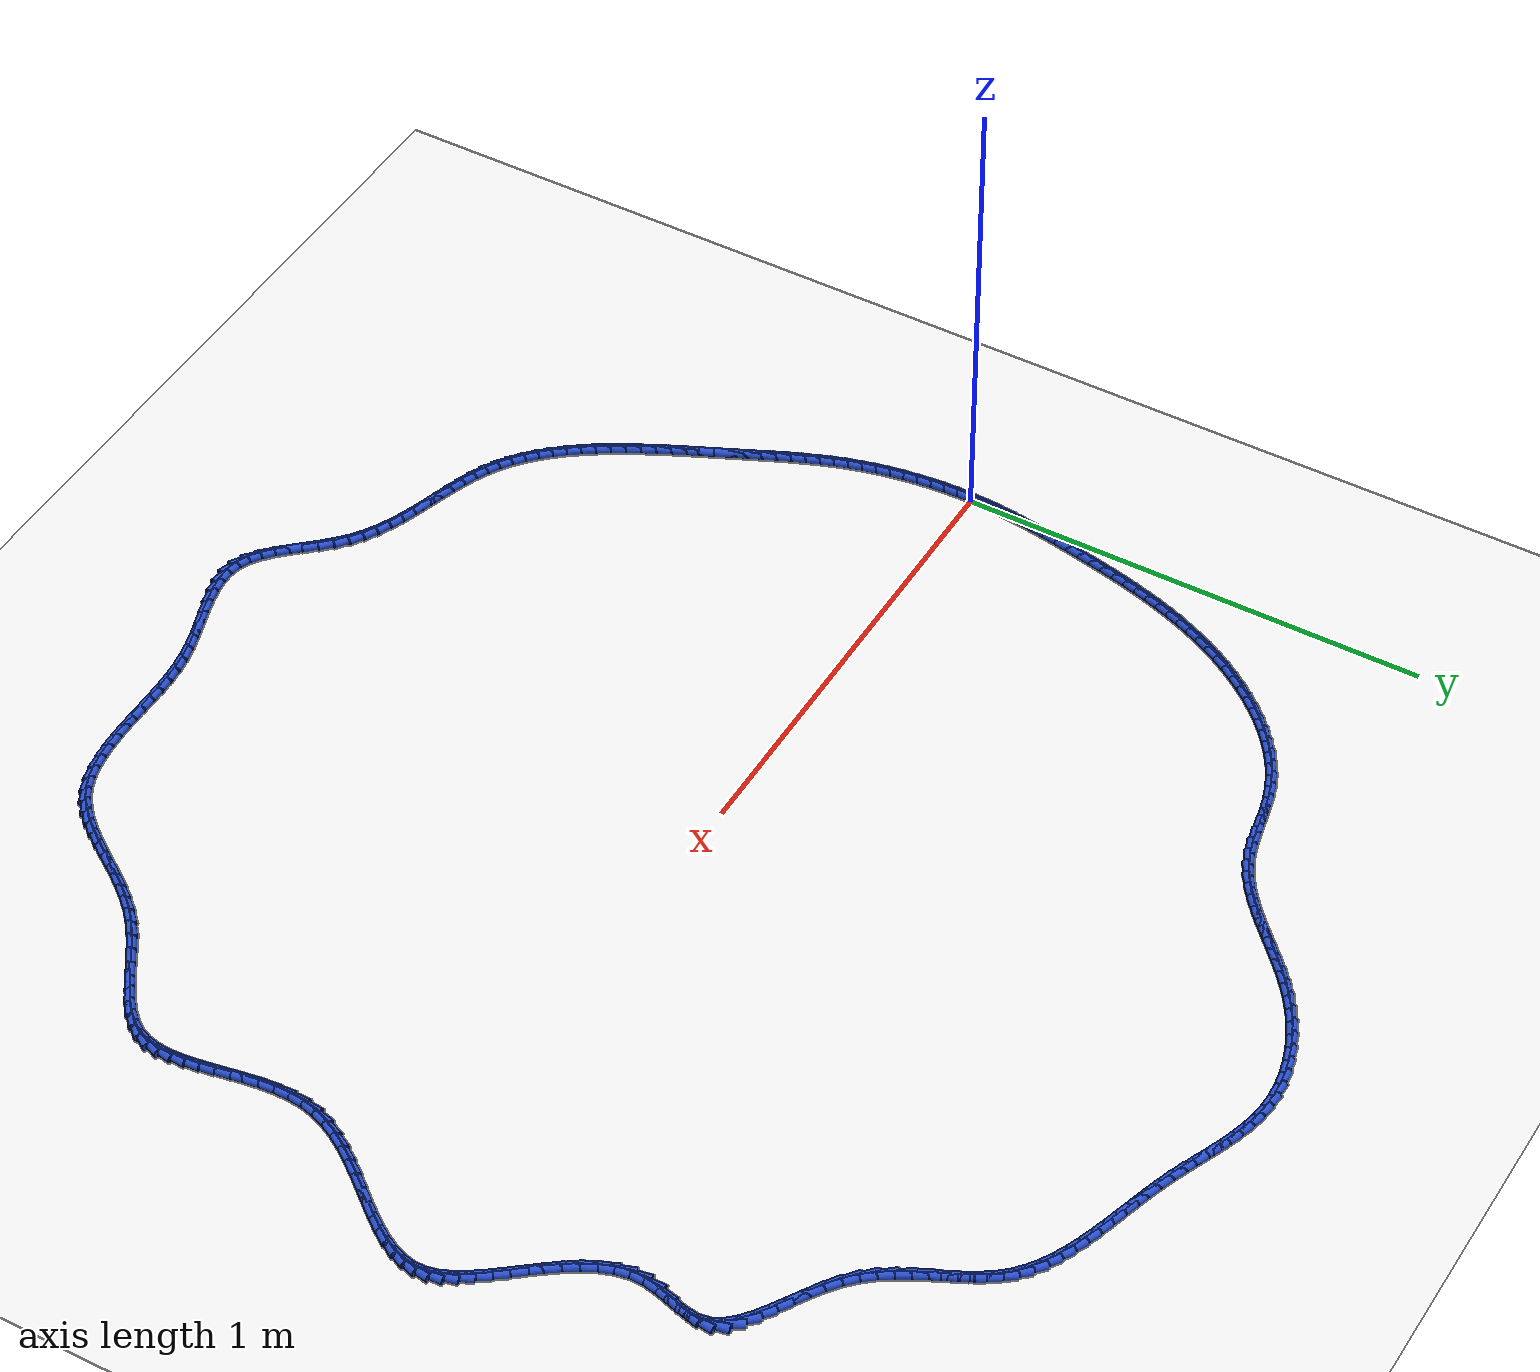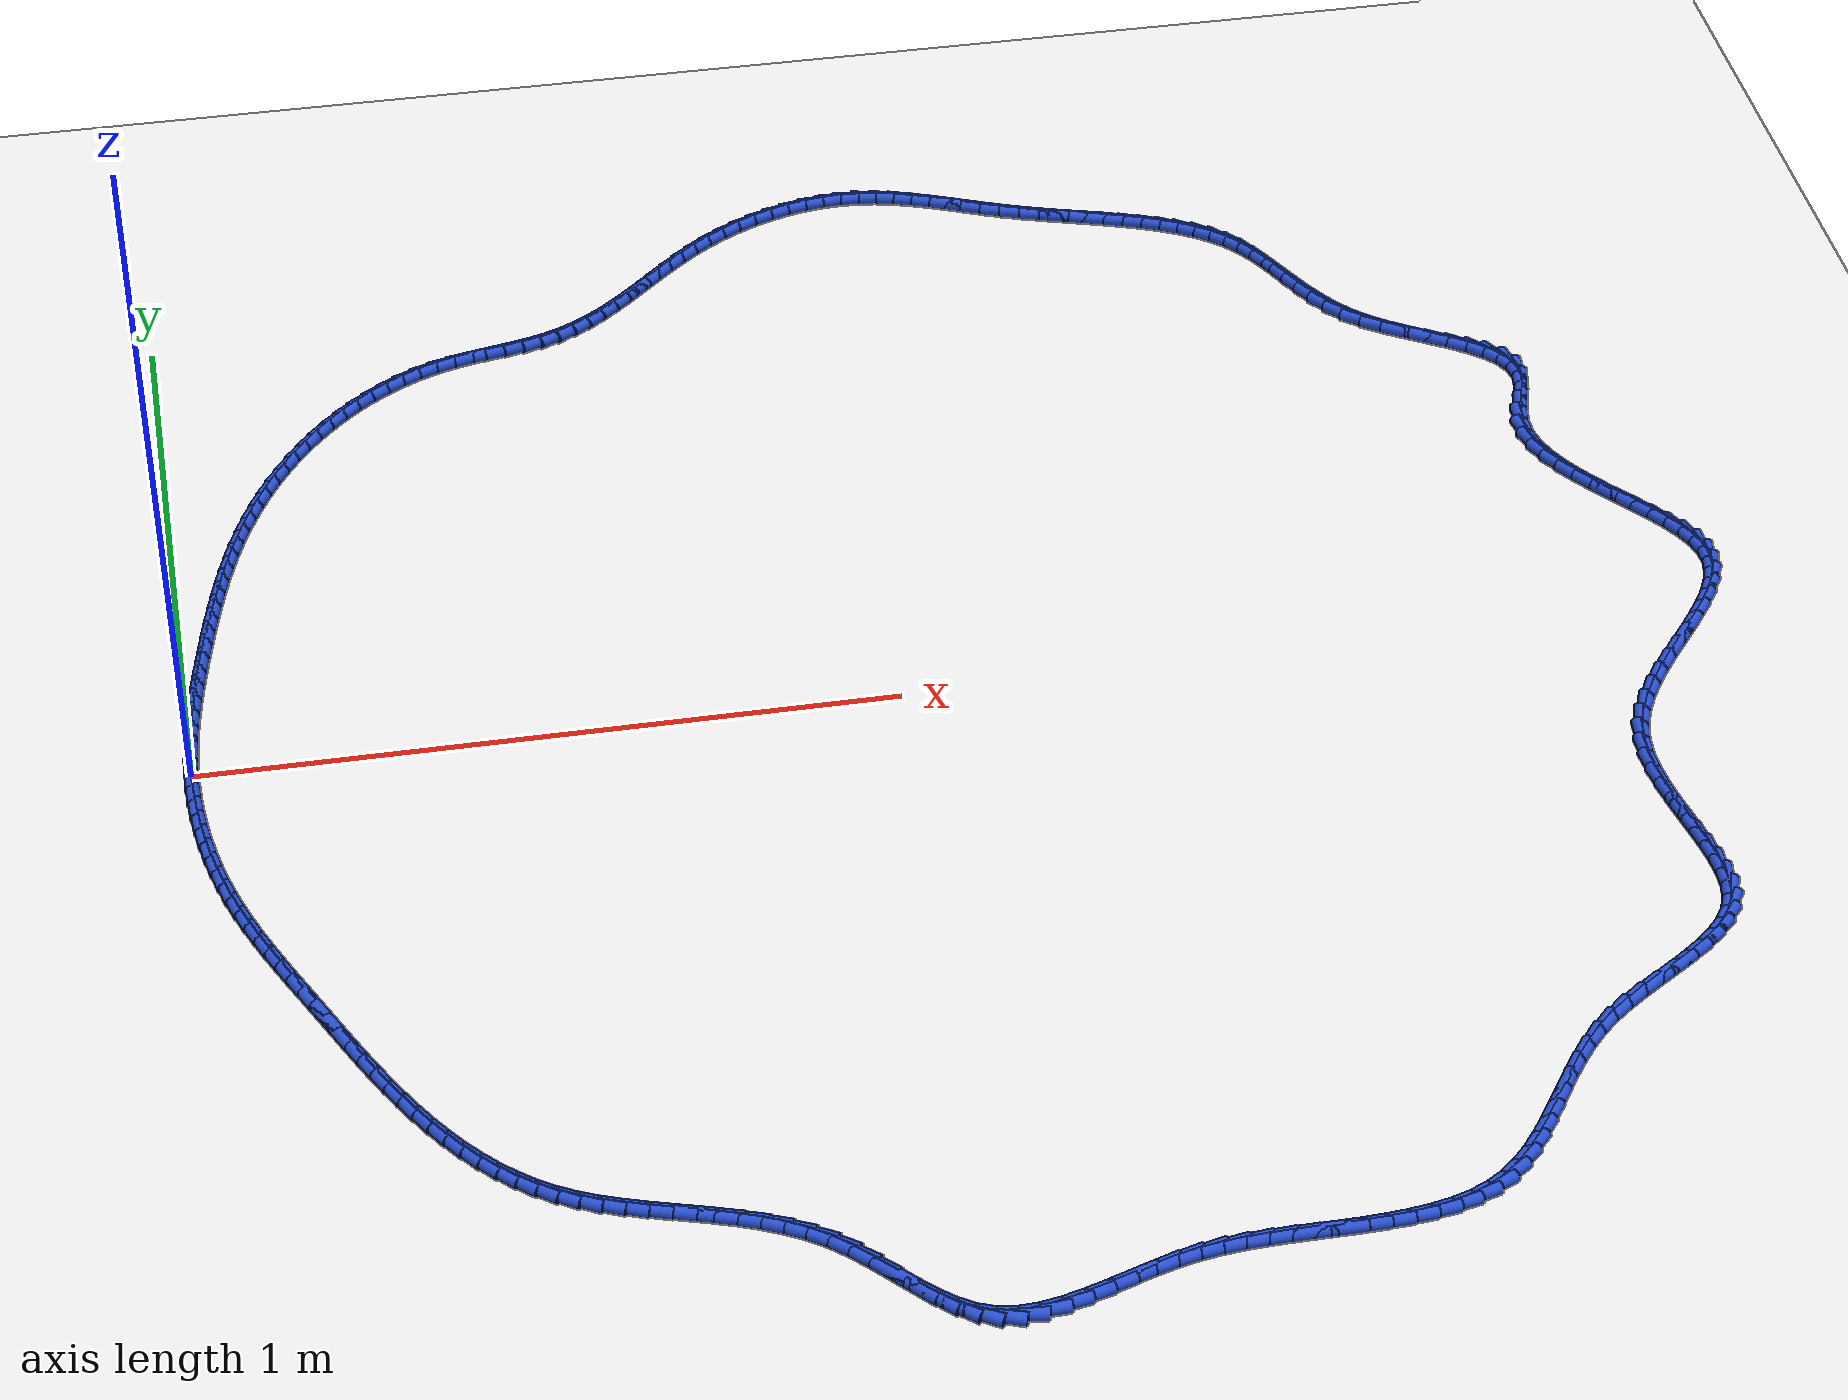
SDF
<sdf version="1.6">
 <world name="default">
  <light name="sun" type="directional">
   <pose>0 0 10 0 -0 0</pose>
   <diffuse>0.8 0.8 0.8 1</diffuse>
   <specular>0.2 0.2 0.2 1</specular>
   <attenuation>
    <range>1000</range>
    <constant>0.9</constant>
    <linear>0.01</linear>
    <quadratic>0.001</quadratic>
   </attenuation>
   <direction>-0.5 0.1 -0.9</direction>
  </light>
  <model name="ground_plane">
   <static>1</static>
   <link name="link">
    <collision name="collision">
     <geometry><plane><normal>0 0 1</normal><size>100 100</size></plane></geometry>
     <surface><friction><ode><mu>100</mu><mu2>50</mu2></ode></friction></surface>
    </collision>
    <visual name="visual">
     <cast_shadows>0</cast_shadows>
     <geometry><plane><normal>0 0 1</normal><size>100 100</size></plane></geometry>
     <material>
      <script><uri>file://media/materials/scripts/gazebo.material</uri><name>Gazebo/WhiteGlow</name></script>
     </material>
    </visual>
   </link>
  </model>
  <gravity>0 0 -9.8</gravity>
  <magnetic_field>6e-06 2.3e-05 -4.2e-05</magnetic_field>
  <atmosphere type="adiabatic"/>
  <physics name="default_physics" default="0" type="ode">
   <max_step_size>0.001</max_step_size>
   <real_time_factor>1</real_time_factor>
   <real_time_update_rate>1000</real_time_update_rate>
  </physics>
  <scene><ambient>0.4 0.4 0.4 1</ambient><background>0.7 0.7 0.7 1</background><shadows>1</shadows></scene>
  <spherical_coordinates>
   <surface_model>EARTH_WGS84</surface_model>
   <latitude_deg>0</latitude_deg>
   <longitude_deg>0</longitude_deg>
   <elevation>0</elevation>
   <heading_deg>0</heading_deg>
  </spherical_coordinates>
  <model name="line">
   <link name="link_0">
    <pose>-5.204170427930421e-18 1.3877787807814457e-17 0.01 0 1.57 1.5329400787040186</pose>
    <collision name="collision">
     <geometry><cylinder><radius>0.01</radius><length>0.08</length></cylinder></geometry>
    </collision>
    <visual name="visual">
     <material>
      <script><name>Gazebo/Blue</name><uri>file://media/materials/scripts/gazebo.material</uri></script>
     </material>
     <geometry><cylinder><radius>0.01</radius><length>0.08</length></cylinder></geometry>
    </visual>
   </link>
   <link name="link_1">
    <pose>0.0011373522767443292 0.030029624452386987 0.01 0 1.57 1.5011955594375406</pose>
    <collision name="collision">
     <geometry><cylinder><radius>0.01</radius><length>0.08</length></cylinder></geometry>
    </collision>
    <visual name="visual">
     <material>
      <script><name>Gazebo/Blue</name><uri>file://media/materials/scripts/gazebo.material</uri></script>
     </material>
     <geometry><cylinder><radius>0.01</radius><length>0.08</length></cylinder></geometry>
    </visual>
   </link>
   <link name="link_2">
    <pose>0.0032239314309353037 0.05996045466123885 0.01 0 1.57 1.4728184669057203</pose>
    <collision name="collision">
     <geometry><cylinder><radius>0.01</radius><length>0.08</length></cylinder></geometry>
    </collision>
    <visual name="visual">
     <material>
      <script><name>Gazebo/Blue</name><uri>file://media/materials/scripts/gazebo.material</uri></script>
     </material>
     <geometry><cylinder><radius>0.01</radius><length>0.08</length></cylinder></geometry>
    </visual>
   </link>
   <link name="link_3">
    <pose>0.006156769730512951 0.08979829292575754 0.01 0 1.57 1.4478548080208276</pose>
    <collision name="collision">
     <geometry><cylinder><radius>0.01</radius><length>0.08</length></cylinder></geometry>
    </collision>
    <visual name="visual">
     <material>
      <script><name>Gazebo/Blue</name><uri>file://media/materials/scripts/gazebo.material</uri></script>
     </material>
     <geometry><cylinder><radius>0.01</radius><length>0.08</length></cylinder></geometry>
    </visual>
   </link>
   <link name="link_4">
    <pose>0.009832899443417293 0.11954894154514495 0.01 0 1.57 1.426324234562757</pose>
    <collision name="collision">
     <geometry><cylinder><radius>0.01</radius><length>0.08</length></cylinder></geometry>
    </collision>
    <visual name="visual">
     <material>
      <script><name>Gazebo/Blue</name><uri>file://media/materials/scripts/gazebo.material</uri></script>
     </material>
     <geometry><cylinder><radius>0.01</radius><length>0.08</length></cylinder></geometry>
    </visual>
   </link>
   <link name="link_5">
    <pose>0.014149352837588365 0.14921820281860312 0.01 0 1.57 1.408228670041951</pose>
    <collision name="collision">
     <geometry><cylinder><radius>0.01</radius><length>0.08</length></cylinder></geometry>
    </collision>
    <visual name="visual">
     <material>
      <script><name>Gazebo/Blue</name><uri>file://media/materials/scripts/gazebo.material</uri></script>
     </material>
     <geometry><cylinder><radius>0.01</radius><length>0.08</length></cylinder></geometry>
    </visual>
   </link>
   <link name="link_6">
    <pose>0.0190031621809662 0.17881187904533402 0.01 0 1.57 1.3935599136054329</pose>
    <collision name="collision">
     <geometry><cylinder><radius>0.01</radius><length>0.08</length></cylinder></geometry>
    </collision>
    <visual name="visual">
     <material>
      <script><name>Gazebo/Blue</name><uri>file://media/materials/scripts/gazebo.material</uri></script>
     </material>
     <geometry><cylinder><radius>0.01</radius><length>0.08</length></cylinder></geometry>
    </visual>
   </link>
   <link name="link_7">
    <pose>0.02429135974149082 0.2083357725245395 0.01 0 1.57 1.382306038179606</pose>
    <collision name="collision">
     <geometry><cylinder><radius>0.01</radius><length>0.08</length></cylinder></geometry>
    </collision>
    <visual name="visual">
     <material>
      <script><name>Gazebo/Blue</name><uri>file://media/materials/scripts/gazebo.material</uri></script>
     </material>
     <geometry><cylinder><radius>0.01</radius><length>0.08</length></cylinder></geometry>
    </visual>
   </link>
   <link name="link_8">
    <pose>0.029910977787102222 0.23779568555542138 0.01 0 1.57 1.3744318169296947</pose>
    <collision name="collision">
     <geometry><cylinder><radius>0.01</radius><length>0.08</length></cylinder></geometry>
    </collision>
    <visual name="visual">
     <material>
      <script><name>Gazebo/Blue</name><uri>file://media/materials/scripts/gazebo.material</uri></script>
     </material>
     <geometry><cylinder><radius>0.01</radius><length>0.08</length></cylinder></geometry>
    </visual>
   </link>
   <link name="link_9">
    <pose>0.03575978455366879 0.2671973226435751 0.01 0 1.57 1.3677673976509888</pose>
    <collision name="collision">
     <geometry><cylinder><radius>0.01</radius><length>0.08</length></cylinder></geometry>
    </collision>
    <visual name="visual">
     <material>
      <script><name>Gazebo/Blue</name><uri>file://media/materials/scripts/gazebo.material</uri></script>
     </material>
     <geometry><cylinder><radius>0.01</radius><length>0.08</length></cylinder></geometry>
    </visual>
   </link>
   <link name="link_10">
    <pose>0.04179997846411434 0.29653782696991726 0.01 0 1.57 1.3584889240832074</pose>
    <collision name="collision">
     <geometry><cylinder><radius>0.01</radius><length>0.08</length></cylinder></geometry>
    </collision>
    <visual name="visual">
     <material>
      <script><name>Gazebo/Blue</name><uri>file://media/materials/scripts/gazebo.material</uri></script>
     </material>
     <geometry><cylinder><radius>0.01</radius><length>0.08</length></cylinder></geometry>
    </visual>
   </link>
   <link name="link_11">
    <pose>0.0481074465343271 0.32579923505494623 0.01 0 1.57 1.3462011860797136</pose>
    <collision name="collision">
     <geometry><cylinder><radius>0.01</radius><length>0.08</length></cylinder></geometry>
    </collision>
    <visual name="visual">
     <material>
      <script><name>Gazebo/Blue</name><uri>file://media/materials/scripts/gazebo.material</uri></script>
     </material>
     <geometry><cylinder><radius>0.01</radius><length>0.08</length></cylinder></geometry>
    </visual>
   </link>
   <link name="link_12">
    <pose>0.05476967076064663 0.3549620427066964 0.01 0 1.57 1.3309022796629506</pose>
    <collision name="collision">
     <geometry><cylinder><radius>0.01</radius><length>0.08</length></cylinder></geometry>
    </collision>
    <visual name="visual">
     <material>
      <script><name>Gazebo/Blue</name><uri>file://media/materials/scripts/gazebo.material</uri></script>
     </material>
     <geometry><cylinder><radius>0.01</radius><length>0.08</length></cylinder></geometry>
    </visual>
   </link>
   <link name="link_13">
    <pose>0.06187413313941233 0.38400674573320115 0.01 0 1.57 1.3125975831280772</pose>
    <collision name="collision">
     <geometry><cylinder><radius>0.01</radius><length>0.08</length></cylinder></geometry>
    </collision>
    <visual name="visual">
     <material>
      <script><name>Gazebo/Blue</name><uri>file://media/materials/scripts/gazebo.material</uri></script>
     </material>
     <geometry><cylinder><radius>0.01</radius><length>0.08</length></cylinder></geometry>
    </visual>
   </link>
   <link name="link_14">
    <pose>0.06950831566696376 0.4129138399424949 0.01 0 1.57 1.2913038914908734</pose>
    <collision name="collision">
     <geometry><cylinder><radius>0.01</radius><length>0.08</length></cylinder></geometry>
    </collision>
    <visual name="visual">
     <material>
      <script><name>Gazebo/Blue</name><uri>file://media/materials/scripts/gazebo.material</uri></script>
     </material>
     <geometry><cylinder><radius>0.01</radius><length>0.08</length></cylinder></geometry>
    </visual>
   </link>
   <link name="link_15">
    <pose>0.07775970033964033 0.44166382114261127 0.01 0 1.57 1.2670542468388943</pose>
    <collision name="collision">
     <geometry><cylinder><radius>0.01</radius><length>0.08</length></cylinder></geometry>
    </collision>
    <visual name="visual">
     <material>
      <script><name>Gazebo/Blue</name><uri>file://media/materials/scripts/gazebo.material</uri></script>
     </material>
     <geometry><cylinder><radius>0.01</radius><length>0.08</length></cylinder></geometry>
    </visual>
   </link>
   <link name="link_16">
    <pose>0.08671576915378161 0.4702371851415844 0.01 0 1.57 1.2399032932530805</pose>
    <collision name="collision">
     <geometry><cylinder><radius>0.01</radius><length>0.08</length></cylinder></geometry>
    </collision>
    <visual name="visual">
     <material>
      <script><name>Gazebo/Blue</name><uri>file://media/materials/scripts/gazebo.material</uri></script>
     </material>
     <geometry><cylinder><radius>0.01</radius><length>0.08</length></cylinder></geometry>
    </visual>
   </link>
   <link name="link_17">
    <pose>0.09646400410572702 0.49861442774744824 0.01 0 1.57 1.2099328810886505</pose>
    <collision name="collision">
     <geometry><cylinder><radius>0.01</radius><length>0.08</length></cylinder></geometry>
    </collision>
    <visual name="visual">
     <material>
      <script><name>Gazebo/Blue</name><uri>file://media/materials/scripts/gazebo.material</uri></script>
     </material>
     <geometry><cylinder><radius>0.01</radius><length>0.08</length></cylinder></geometry>
    </visual>
   </link>
   <link name="link_18">
    <pose>0.10709188719181606 0.5267760447682367 0.01 0 1.57 1.1772575251762634</pose>
    <collision name="collision">
     <geometry><cylinder><radius>0.01</radius><length>0.08</length></cylinder></geometry>
    </collision>
    <visual name="visual">
     <material>
      <script><name>Gazebo/Blue</name><uri>file://media/materials/scripts/gazebo.material</uri></script>
     </material>
     <geometry><cylinder><radius>0.01</radius><length>0.08</length></cylinder></geometry>
    </visual>
   </link>
   <link name="link_19">
    <pose>0.11868690040838828 0.5547025320119839 0.01 0 1.57 1.1420292014586377</pose>
    <collision name="collision">
     <geometry><cylinder><radius>0.01</radius><length>0.08</length></cylinder></geometry>
    </collision>
    <visual name="visual">
     <material>
      <script><name>Gazebo/Blue</name><uri>file://media/materials/scripts/gazebo.material</uri></script>
     </material>
     <geometry><cylinder><radius>0.01</radius><length>0.08</length></cylinder></geometry>
    </visual>
   </link>
   <link name="link_20">
    <pose>0.13133652575178312 0.5823743852867238 0.01 0 1.57 1.104446775173002</pose>
    <collision name="collision">
     <geometry><cylinder><radius>0.01</radius><length>0.08</length></cylinder></geometry>
    </collision>
    <visual name="visual">
     <material>
      <script><name>Gazebo/Blue</name><uri>file://media/materials/scripts/gazebo.material</uri></script>
     </material>
     <geometry><cylinder><radius>0.01</radius><length>0.08</length></cylinder></geometry>
    </visual>
   </link>
   <link name="link_21">
    <pose>0.14512775174061754 0.6097715227254505 0.01 0 1.57 1.065118207337849</pose>
    <collision name="collision">
     <geometry><cylinder><radius>0.01</radius><length>0.08</length></cylinder></geometry>
    </collision>
    <visual name="visual">
     <material>
      <script><name>Gazebo/Blue</name><uri>file://media/materials/scripts/gazebo.material</uri></script>
     </material>
     <geometry><cylinder><radius>0.01</radius><length>0.08</length></cylinder></geometry>
    </visual>
   </link>
   <link name="link_22">
    <pose>0.16010977241079943 0.6368296194724666 0.01 0 1.57 1.0245831309131712</pose>
    <collision name="collision">
     <geometry><cylinder><radius>0.01</radius><length>0.08</length></cylinder></geometry>
    </collision>
    <visual name="visual">
     <material>
      <script><name>Gazebo/Blue</name><uri>file://media/materials/scripts/gazebo.material</uri></script>
     </material>
     <geometry><cylinder><radius>0.01</radius><length>0.08</length></cylinder></geometry>
    </visual>
   </link>
   <link name="link_23">
    <pose>0.17626793475277147 0.663409610024551 0.01 0 1.57 0.9825336282329492</pose>
    <collision name="collision">
     <geometry><cylinder><radius>0.01</radius><length>0.08</length></cylinder></geometry>
    </collision>
    <visual name="visual">
     <material>
      <script><name>Gazebo/Blue</name><uri>file://media/materials/scripts/gazebo.material</uri></script>
     </material>
     <geometry><cylinder><radius>0.01</radius><length>0.08</length></cylinder></geometry>
    </visual>
   </link>
   <link name="link_24">
    <pose>0.1935814283915461 0.6893652209415141 0.01 0 1.57 0.9385887634483274</pose>
    <collision name="collision">
     <geometry><cylinder><radius>0.01</radius><length>0.08</length></cylinder></geometry>
    </collision>
    <visual name="visual">
     <material>
      <script><name>Gazebo/Blue</name><uri>file://media/materials/scripts/gazebo.material</uri></script>
     </material>
     <geometry><cylinder><radius>0.01</radius><length>0.08</length></cylinder></geometry>
    </visual>
   </link>
   <link name="link_25">
    <pose>0.21202944295213538 0.7145501787831661 0.01 0 1.57 0.8923652811128439</pose>
    <collision name="collision">
     <geometry><cylinder><radius>0.01</radius><length>0.08</length></cylinder></geometry>
    </collision>
    <visual name="visual">
     <material>
      <script><name>Gazebo/Blue</name><uri>file://media/materials/scripts/gazebo.material</uri></script>
     </material>
     <geometry><cylinder><radius>0.01</radius><length>0.08</length></cylinder></geometry>
    </visual>
   </link>
   <link name="link_26">
    <pose>0.23159116805955188 0.738818210109318 0.01 0 1.57 0.843477723860848</pose>
    <collision name="collision">
     <geometry><cylinder><radius>0.01</radius><length>0.08</length></cylinder></geometry>
    </collision>
    <visual name="visual">
     <material>
      <script><name>Gazebo/Blue</name><uri>file://media/materials/scripts/gazebo.material</uri></script>
     </material>
     <geometry><cylinder><radius>0.01</radius><length>0.08</length></cylinder></geometry>
    </visual>
   </link>
   <link name="link_27">
    <pose>0.2522457933388077 0.7620230414797797 0.01 0 1.57 0.7915424172978874</pose>
    <collision name="collision">
     <geometry><cylinder><radius>0.01</radius><length>0.08</length></cylinder></geometry>
    </collision>
    <visual name="visual">
     <material>
      <script><name>Gazebo/Blue</name><uri>file://media/materials/scripts/gazebo.material</uri></script>
     </material>
     <geometry><cylinder><radius>0.01</radius><length>0.08</length></cylinder></geometry>
    </visual>
   </link>
   <link name="link_28">
    <pose>0.2739725084149154 0.7840183994543622 0.01 0 1.57 0.7361864022791854</pose>
    <collision name="collision">
     <geometry><cylinder><radius>0.01</radius><length>0.08</length></cylinder></geometry>
    </collision>
    <visual name="visual">
     <material>
      <script><name>Gazebo/Blue</name><uri>file://media/materials/scripts/gazebo.material</uri></script>
     </material>
     <geometry><cylinder><radius>0.01</radius><length>0.08</length></cylinder></geometry>
    </visual>
   </link>
   <link name="link_29">
    <pose>0.29675050291288707 0.804658010592876 0.01 0 1.57 0.6770626002389787</pose>
    <collision name="collision">
     <geometry><cylinder><radius>0.01</radius><length>0.08</length></cylinder></geometry>
    </collision>
    <visual name="visual">
     <material>
      <script><name>Gazebo/Blue</name><uri>file://media/materials/scripts/gazebo.material</uri></script>
     </material>
     <geometry><cylinder><radius>0.01</radius><length>0.08</length></cylinder></geometry>
    </visual>
   </link>
   <link name="link_30">
    <pose>0.32055896645773513 0.8237956014551316 0.01 0 1.57 0.6138724626696549</pose>
    <collision name="collision">
     <geometry><cylinder><radius>0.01</radius><length>0.08</length></cylinder></geometry>
    </collision>
    <visual name="visual">
     <material>
      <script><name>Gazebo/Blue</name><uri>file://media/materials/scripts/gazebo.material</uri></script>
     </material>
     <geometry><cylinder><radius>0.01</radius><length>0.08</length></cylinder></geometry>
    </visual>
   </link>
   <link name="link_31">
    <pose>0.34537708867447187 0.8412848986009391 0.01 0 1.57 0.5463968542924611</pose>
    <collision name="collision">
     <geometry><cylinder><radius>0.01</radius><length>0.08</length></cylinder></geometry>
    </collision>
    <visual name="visual">
     <material>
      <script><name>Gazebo/Blue</name><uri>file://media/materials/scripts/gazebo.material</uri></script>
     </material>
     <geometry><cylinder><radius>0.01</radius><length>0.08</length></cylinder></geometry>
    </visual>
   </link>
   <link name="link_32">
    <pose>0.3711840591881098 0.8569796285901098 0.01 0 1.57 0.4745346650176418</pose>
    <collision name="collision">
     <geometry><cylinder><radius>0.01</radius><length>0.08</length></cylinder></geometry>
    </collision>
    <visual name="visual">
     <material>
      <script><name>Gazebo/Blue</name><uri>file://media/materials/scripts/gazebo.material</uri></script>
     </material>
     <geometry><cylinder><radius>0.01</radius><length>0.08</length></cylinder></geometry>
    </visual>
   </link>
   <link name="link_33">
    <pose>0.39795906762366096 0.8707335179824534 0.01 0 1.57 0.3983464035240839</pose>
    <collision name="collision">
     <geometry><cylinder><radius>0.01</radius><length>0.08</length></cylinder></geometry>
    </collision>
    <visual name="visual">
     <material>
      <script><name>Gazebo/Blue</name><uri>file://media/materials/scripts/gazebo.material</uri></script>
     </material>
     <geometry><cylinder><radius>0.01</radius><length>0.08</length></cylinder></geometry>
    </visual>
   </link>
   <link name="link_34">
    <pose>0.42568130360613776 0.8824002933377809 0.01 0 1.57 0.3184755314834646</pose>
    <collision name="collision">
     <geometry><cylinder><radius>0.01</radius><length>0.08</length></cylinder></geometry>
    </collision>
    <visual name="visual">
     <material>
      <script><name>Gazebo/Blue</name><uri>file://media/materials/scripts/gazebo.material</uri></script>
     </material>
     <geometry><cylinder><radius>0.01</radius><length>0.08</length></cylinder></geometry>
    </visual>
   </link>
   <link name="link_35">
    <pose>0.4543258373528002 0.8918443495432264 0.01 0 1.57 0.24999352496729918</pose>
    <collision name="collision">
     <geometry><cylinder><radius>0.01</radius><length>0.08</length></cylinder></geometry>
    </collision>
    <visual name="visual">
     <material>
      <script><name>Gazebo/Blue</name><uri>file://media/materials/scripts/gazebo.material</uri></script>
     </material>
     <geometry><cylinder><radius>0.01</radius><length>0.08</length></cylinder></geometry>
    </visual>
   </link>
   <link name="link_36">
    <pose>0.48370698933660045 0.8993463866910646 0.01 0 1.57 0.21151882604593314</pose>
    <collision name="collision">
     <geometry><cylinder><radius>0.01</radius><length>0.08</length></cylinder></geometry>
    </collision>
    <visual name="visual">
     <material>
      <script><name>Gazebo/Blue</name><uri>file://media/materials/scripts/gazebo.material</uri></script>
     </material>
     <geometry><cylinder><radius>0.01</radius><length>0.08</length></cylinder></geometry>
    </visual>
   </link>
   <link name="link_37">
    <pose>0.5134299081417895 0.9057288123979677 0.01 0 1.57 0.20355974306977132</pose>
    <collision name="collision">
     <geometry><cylinder><radius>0.01</radius><length>0.08</length></cylinder></geometry>
    </collision>
    <visual name="visual">
     <material>
      <script><name>Gazebo/Blue</name><uri>file://media/materials/scripts/gazebo.material</uri></script>
     </material>
     <geometry><cylinder><radius>0.01</radius><length>0.08</length></cylinder></geometry>
    </visual>
   </link>
   <link name="link_38">
    <pose>0.5430857275500556 0.9118503294254631 0.01 0 1.57 0.2263269611646624</pose>
    <collision name="collision">
     <geometry><cylinder><radius>0.01</radius><length>0.08</length></cylinder></geometry>
    </collision>
    <visual name="visual">
     <material>
      <script><name>Gazebo/Blue</name><uri>file://media/materials/scripts/gazebo.material</uri></script>
     </material>
     <geometry><cylinder><radius>0.01</radius><length>0.08</length></cylinder></geometry>
    </visual>
   </link>
   <link name="link_39">
    <pose>0.5722655813430882 0.918569640535079 0.01 0 1.57 0.2812873443849104</pose>
    <collision name="collision">
     <geometry><cylinder><radius>0.01</radius><length>0.08</length></cylinder></geometry>
    </collision>
    <visual name="visual">
     <material>
      <script><name>Gazebo/Blue</name><uri>file://media/materials/scripts/gazebo.material</uri></script>
     </material>
     <geometry><cylinder><radius>0.01</radius><length>0.08</length></cylinder></geometry>
    </visual>
   </link>
   <link name="link_40">
    <pose>0.600560603302576 0.9267454484883436 0.01 0 1.57 0.37011426301411954</pose>
    <collision name="collision">
     <geometry><cylinder><radius>0.01</radius><length>0.08</length></cylinder></geometry>
    </collision>
    <visual name="visual">
     <material>
      <script><name>Gazebo/Blue</name><uri>file://media/materials/scripts/gazebo.material</uri></script>
     </material>
     <geometry><cylinder><radius>0.01</radius><length>0.08</length></cylinder></geometry>
    </visual>
   </link>
   <link name="link_41">
    <pose>0.6275683668522558 0.9372243154432224 0.01 0 1.57 0.47386962115481096</pose>
    <collision name="collision">
     <geometry><cylinder><radius>0.01</radius><length>0.08</length></cylinder></geometry>
    </collision>
    <visual name="visual">
     <material>
      <script><name>Gazebo/Blue</name><uri>file://media/materials/scripts/gazebo.material</uri></script>
     </material>
     <geometry><cylinder><radius>0.01</radius><length>0.08</length></cylinder></geometry>
    </visual>
   </link>
   <link name="link_42">
    <pose>0.6531551014019836 0.9503463086627927 0.01 0 1.57 0.5639347500437251</pose>
    <collision name="collision">
     <geometry><cylinder><radius>0.01</radius><length>0.08</length></cylinder></geometry>
    </collision>
    <visual name="visual">
     <material>
      <script><name>Gazebo/Blue</name><uri>file://media/materials/scripts/gazebo.material</uri></script>
     </material>
     <geometry><cylinder><radius>0.01</radius><length>0.08</length></cylinder></geometry>
    </visual>
   </link>
   <link name="link_43">
    <pose>0.6775470113462687 0.9657728375672602 0.01 0 1.57 0.6368800323419674</pose>
    <collision name="collision">
     <geometry><cylinder><radius>0.01</radius><length>0.08</length></cylinder></geometry>
    </collision>
    <visual name="visual">
     <material>
      <script><name>Gazebo/Blue</name><uri>file://media/materials/scripts/gazebo.material</uri></script>
     </material>
     <geometry><cylinder><radius>0.01</radius><length>0.08</length></cylinder></geometry>
    </visual>
   </link>
   <link name="link_44">
    <pose>0.7009954961072249 0.9831178116009573 0.01 0 1.57 0.6924937310259418</pose>
    <collision name="collision">
     <geometry><cylinder><radius>0.01</radius><length>0.08</length></cylinder></geometry>
    </collision>
    <visual name="visual">
     <material>
      <script><name>Gazebo/Blue</name><uri>file://media/materials/scripts/gazebo.material</uri></script>
     </material>
     <geometry><cylinder><radius>0.01</radius><length>0.08</length></cylinder></geometry>
    </visual>
   </link>
   <link name="link_45">
    <pose>0.7237519551069673 1.0019951402082168 0.01 0 1.57 0.7313113552406284</pose>
    <collision name="collision">
     <geometry><cylinder><radius>0.01</radius><length>0.08</length></cylinder></geometry>
    </collision>
    <visual name="visual">
     <material>
      <script><name>Gazebo/Blue</name><uri>file://media/materials/scripts/gazebo.material</uri></script>
     </material>
     <geometry><cylinder><radius>0.01</radius><length>0.08</length></cylinder></geometry>
    </visual>
   </link>
   <link name="link_46">
    <pose>0.7460677877676102 1.0220187328333719 0.01 0 1.57 0.7541143152115496</pose>
    <collision name="collision">
     <geometry><cylinder><radius>0.01</radius><length>0.08</length></cylinder></geometry>
    </collision>
    <visual name="visual">
     <material>
      <script><name>Gazebo/Blue</name><uri>file://media/materials/scripts/gazebo.material</uri></script>
     </material>
     <geometry><cylinder><radius>0.01</radius><length>0.08</length></cylinder></geometry>
    </visual>
   </link>
   <link name="link_47">
    <pose>0.7681943935112682 1.0428024989207547 0.01 0 1.57 0.7616192674383127</pose>
    <collision name="collision">
     <geometry><cylinder><radius>0.01</radius><length>0.08</length></cylinder></geometry>
    </collision>
    <visual name="visual">
     <material>
      <script><name>Gazebo/Blue</name><uri>file://media/materials/scripts/gazebo.material</uri></script>
     </material>
     <geometry><cylinder><radius>0.01</radius><length>0.08</length></cylinder></geometry>
    </visual>
   </link>
   <link name="link_48">
    <pose>0.7903831717600556 1.0639603479146982 0.01 0 1.57 0.7543299265297234</pose>
    <collision name="collision">
     <geometry><cylinder><radius>0.01</radius><length>0.08</length></cylinder></geometry>
    </collision>
    <visual name="visual">
     <material>
      <script><name>Gazebo/Blue</name><uri>file://media/materials/scripts/gazebo.material</uri></script>
     </material>
     <geometry><cylinder><radius>0.01</radius><length>0.08</length></cylinder></geometry>
    </visual>
   </link>
   <link name="link_49">
    <pose>0.8128855219360867 1.0851061892595348 0.01 0 1.57 0.7325073360217118</pose>
    <collision name="collision">
     <geometry><cylinder><radius>0.01</radius><length>0.08</length></cylinder></geometry>
    </collision>
    <visual name="visual">
     <material>
      <script><name>Gazebo/Blue</name><uri>file://media/materials/scripts/gazebo.material</uri></script>
     </material>
     <geometry><cylinder><radius>0.01</radius><length>0.08</length></cylinder></geometry>
    </visual>
   </link>
   <link name="link_50">
    <pose>0.8359528434614767 1.1058539323995975 0.01 0 1.57 0.6962308092457923</pose>
    <collision name="collision">
     <geometry><cylinder><radius>0.01</radius><length>0.08</length></cylinder></geometry>
    </collision>
    <visual name="visual">
     <material>
      <script><name>Gazebo/Blue</name><uri>file://media/materials/scripts/gazebo.material</uri></script>
     </material>
     <geometry><cylinder><radius>0.01</radius><length>0.08</length></cylinder></geometry>
    </visual>
   </link>
   <link name="link_51">
    <pose>0.8598365357583396 1.125817486779219 0.01 0 1.57 0.6455421104442264</pose>
    <collision name="collision">
     <geometry><cylinder><radius>0.01</radius><length>0.08</length></cylinder></geometry>
    </collision>
    <visual name="visual">
     <material>
      <script><name>Gazebo/Blue</name><uri>file://media/materials/scripts/gazebo.material</uri></script>
     </material>
     <geometry><cylinder><radius>0.01</radius><length>0.08</length></cylinder></geometry>
    </visual>
   </link>
   <link name="link_52">
    <pose>0.8847879854943734 1.1446107679804778 0.01 0 1.57 0.5833823803697511</pose>
    <collision name="collision">
     <geometry><cylinder><radius>0.01</radius><length>0.08</length></cylinder></geometry>
    </collision>
    <visual name="visual">
     <material>
      <script><name>Gazebo/Blue</name><uri>file://media/materials/scripts/gazebo.material</uri></script>
     </material>
     <geometry><cylinder><radius>0.01</radius><length>0.08</length></cylinder></geometry>
    </visual>
   </link>
   <link name="link_53">
    <pose>0.910969183622218 1.1618907110521919 0.01 0 1.57 0.5187806332710961</pose>
    <collision name="collision">
     <geometry><cylinder><radius>0.01</radius><length>0.08</length></cylinder></geometry>
    </collision>
    <visual name="visual">
     <material>
      <script><name>Gazebo/Blue</name><uri>file://media/materials/scripts/gazebo.material</uri></script>
     </material>
     <geometry><cylinder><radius>0.01</radius><length>0.08</length></cylinder></geometry>
    </visual>
   </link>
   <link name="link_54">
    <pose>0.9382388816818173 1.1774601774762277 0.01 0 1.57 0.45268795659579786</pose>
    <collision name="collision">
     <geometry><cylinder><radius>0.01</radius><length>0.08</length></cylinder></geometry>
    </collision>
    <visual name="visual">
     <material>
      <script><name>Gazebo/Blue</name><uri>file://media/materials/scripts/gazebo.material</uri></script>
     </material>
     <geometry><cylinder><radius>0.01</radius><length>0.08</length></cylinder></geometry>
    </visual>
   </link>
   <link name="link_55">
    <pose>0.9663915949534007 1.19115294083842 0.01 0 1.57 0.38402191226503923</pose>
    <collision name="collision">
     <geometry><cylinder><radius>0.01</radius><length>0.08</length></cylinder></geometry>
    </collision>
    <visual name="visual">
     <material>
      <script><name>Gazebo/Blue</name><uri>file://media/materials/scripts/gazebo.material</uri></script>
     </material>
     <geometry><cylinder><radius>0.01</radius><length>0.08</length></cylinder></geometry>
    </visual>
   </link>
   <link name="link_56">
    <pose>0.9952218387171993 1.2028027747246057 0.01 0 1.57 0.3116812465148708</pose>
    <collision name="collision">
     <geometry><cylinder><radius>0.01</radius><length>0.08</length></cylinder></geometry>
    </collision>
    <visual name="visual">
     <material>
      <script><name>Gazebo/Blue</name><uri>file://media/materials/scripts/gazebo.material</uri></script>
     </material>
     <geometry><cylinder><radius>0.01</radius><length>0.08</length></cylinder></geometry>
    </visual>
   </link>
   <link name="link_57">
    <pose>1.0245241282534419 1.2122434527206178 0.01 0 1.57 0.23454613481737252</pose>
    <collision name="collision">
     <geometry><cylinder><radius>0.01</radius><length>0.08</length></cylinder></geometry>
    </collision>
    <visual name="visual">
     <material>
      <script><name>Gazebo/Blue</name><uri>file://media/materials/scripts/gazebo.material</uri></script>
     </material>
     <geometry><cylinder><radius>0.01</radius><length>0.08</length></cylinder></geometry>
    </visual>
   </link>
   <link name="link_58">
    <pose>1.0540929788423585 1.2193087484122926 0.01 0 1.57 0.15150300358352195</pose>
    <collision name="collision">
     <geometry><cylinder><radius>0.01</radius><length>0.08</length></cylinder></geometry>
    </collision>
    <visual name="visual">
     <material>
      <script><name>Gazebo/Blue</name><uri>file://media/materials/scripts/gazebo.material</uri></script>
     </material>
     <geometry><cylinder><radius>0.01</radius><length>0.08</length></cylinder></geometry>
    </visual>
   </link>
   <link name="link_59">
    <pose>1.0837229057641797 1.2238324353854655 0.01 0 1.57 0.06150685175452811</pose>
    <collision name="collision">
     <geometry><cylinder><radius>0.01</radius><length>0.08</length></cylinder></geometry>
    </collision>
    <visual name="visual">
     <material>
      <script><name>Gazebo/Blue</name><uri>file://media/materials/scripts/gazebo.material</uri></script>
     </material>
     <geometry><cylinder><radius>0.01</radius><length>0.08</length></cylinder></geometry>
    </visual>
   </link>
   <link name="link_60">
    <pose>1.113208424299135 1.2256482872259706 0.01 0 1.57 -0.03630417214746851</pose>
    <collision name="collision">
     <geometry><cylinder><radius>0.01</radius><length>0.08</length></cylinder></geometry>
    </collision>
    <visual name="visual">
     <material>
      <script><name>Gazebo/Blue</name><uri>file://media/materials/scripts/gazebo.material</uri></script>
     </material>
     <geometry><cylinder><radius>0.01</radius><length>0.08</length></cylinder></geometry>
    </visual>
   </link>
   <link name="link_61">
    <pose>1.142344049727454 1.2245900775196437 0.01 0 1.57 -0.13870744743476215</pose>
    <collision name="collision">
     <geometry><cylinder><radius>0.01</radius><length>0.08</length></cylinder></geometry>
    </collision>
    <visual name="visual">
     <material>
      <script><name>Gazebo/Blue</name><uri>file://media/materials/scripts/gazebo.material</uri></script>
     </material>
     <geometry><cylinder><radius>0.01</radius><length>0.08</length></cylinder></geometry>
    </visual>
   </link>
   <link name="link_62">
    <pose>1.1709801797506125 1.220592361715455 0.01 0 1.57 -0.2285328874764467</pose>
    <collision name="collision">
     <geometry><cylinder><radius>0.01</radius><length>0.08</length></cylinder></geometry>
    </collision>
    <visual name="visual">
     <material>
      <script><name>Gazebo/Blue</name><uri>file://media/materials/scripts/gazebo.material</uri></script>
     </material>
     <geometry><cylinder><radius>0.01</radius><length>0.08</length></cylinder></geometry>
    </visual>
   </link>
   <link name="link_63">
    <pose>1.1992093390987844 1.2140263623309016 0.01 0 1.57 -0.2996577794931523</pose>
    <collision name="collision">
     <geometry><cylinder><radius>0.01</radius><length>0.08</length></cylinder></geometry>
    </collision>
    <visual name="visual">
     <material>
      <script><name>Gazebo/Blue</name><uri>file://media/materials/scripts/gazebo.material</uri></script>
     </material>
     <geometry><cylinder><radius>0.01</radius><length>0.08</length></cylinder></geometry>
    </visual>
   </link>
   <link name="link_64">
    <pose>1.2271896140024414 1.2053815396048047 0.01 0 1.57 -0.3516989463908724</pose>
    <collision name="collision">
     <geometry><cylinder><radius>0.01</radius><length>0.08</length></cylinder></geometry>
    </collision>
    <visual name="visual">
     <material>
      <script><name>Gazebo/Blue</name><uri>file://media/materials/scripts/gazebo.material</uri></script>
     </material>
     <geometry><cylinder><radius>0.01</radius><length>0.08</length></cylinder></geometry>
    </visual>
   </link>
   <link name="link_65">
    <pose>1.2550790918361958 1.1951473558393957 0.01 0 1.57 -0.385165419368328</pose>
    <collision name="collision">
     <geometry><cylinder><radius>0.01</radius><length>0.08</length></cylinder></geometry>
    </collision>
    <visual name="visual">
     <material>
      <script><name>Gazebo/Blue</name><uri>file://media/materials/scripts/gazebo.material</uri></script>
     </material>
     <geometry><cylinder><radius>0.01</radius><length>0.08</length></cylinder></geometry>
    </visual>
   </link>
   <link name="link_66">
    <pose>1.2830358599746574 1.1838132733369031 0.01 0 1.57 -0.4008816383495842</pose>
    <collision name="collision">
     <geometry><cylinder><radius>0.01</radius><length>0.08</length></cylinder></geometry>
    </collision>
    <visual name="visual">
     <material>
      <script><name>Gazebo/Blue</name><uri>file://media/materials/scripts/gazebo.material</uri></script>
     </material>
     <geometry><cylinder><radius>0.01</radius><length>0.08</length></cylinder></geometry>
    </visual>
   </link>
   <link name="link_67">
    <pose>1.3112180057924354 1.1718687543995576 0.01 0 1.57 -0.3996479175823724</pose>
    <collision name="collision">
     <geometry><cylinder><radius>0.01</radius><length>0.08</length></cylinder></geometry>
    </collision>
    <visual name="visual">
     <material>
      <script><name>Gazebo/Blue</name><uri>file://media/materials/scripts/gazebo.material</uri></script>
     </material>
     <geometry><cylinder><radius>0.01</radius><length>0.08</length></cylinder></geometry>
    </visual>
   </link>
   <link name="link_68">
    <pose>1.3397836166641408 1.1598032613295886 0.01 0 1.57 -0.38210880384513446</pose>
    <collision name="collision">
     <geometry><cylinder><radius>0.01</radius><length>0.08</length></cylinder></geometry>
    </collision>
    <visual name="visual">
     <material>
      <script><name>Gazebo/Blue</name><uri>file://media/materials/scripts/gazebo.material</uri></script>
     </material>
     <geometry><cylinder><radius>0.01</radius><length>0.08</length></cylinder></geometry>
    </visual>
   </link>
   <link name="link_69">
    <pose>1.3688907799643837 1.1481062564292264 0.01 0 1.57 -0.3503955778418518</pose>
    <collision name="collision">
     <geometry><cylinder><radius>0.01</radius><length>0.08</length></cylinder></geometry>
    </collision>
    <visual name="visual">
     <material>
      <script><name>Gazebo/Blue</name><uri>file://media/materials/scripts/gazebo.material</uri></script>
     </material>
     <geometry><cylinder><radius>0.01</radius><length>0.08</length></cylinder></geometry>
    </visual>
   </link>
   <link name="link_70">
    <pose>1.3986723270454977 1.1372217905174389 0.01 0 1.57 -0.32127867489133377</pose>
    <collision name="collision">
     <geometry><cylinder><radius>0.01</radius><length>0.08</length></cylinder></geometry>
    </collision>
    <visual name="visual">
     <material>
      <script><name>Gazebo/Blue</name><uri>file://media/materials/scripts/gazebo.material</uri></script>
     </material>
     <geometry><cylinder><radius>0.01</radius><length>0.08</length></cylinder></geometry>
    </visual>
   </link>
   <link name="link_71">
    <pose>1.4290018775737232 1.1271278399453108 0.01 0 1.57 -0.30398634813245</pose>
    <collision name="collision">
     <geometry><cylinder><radius>0.01</radius><length>0.08</length></cylinder></geometry>
    </collision>
    <visual name="visual">
     <material>
      <script><name>Gazebo/Blue</name><uri>file://media/materials/scripts/gazebo.material</uri></script>
     </material>
     <geometry><cylinder><radius>0.01</radius><length>0.08</length></cylinder></geometry>
    </visual>
   </link>
   <link name="link_72">
    <pose>1.459600819893173 1.117528662183703 0.01 0 1.57 -0.2982603628310052</pose>
    <collision name="collision">
     <geometry><cylinder><radius>0.01</radius><length>0.08</length></cylinder></geometry>
    </collision>
    <visual name="visual">
     <material>
      <script><name>Gazebo/Blue</name><uri>file://media/materials/scripts/gazebo.material</uri></script>
     </material>
     <geometry><cylinder><radius>0.01</radius><length>0.08</length></cylinder></geometry>
    </visual>
   </link>
   <link name="link_73">
    <pose>1.4901886013452763 1.1081250246918721 0.01 0 1.57 -0.3040815012861486</pose>
    <collision name="collision">
     <geometry><cylinder><radius>0.01</radius><length>0.08</length></cylinder></geometry>
    </collision>
    <visual name="visual">
     <material>
      <script><name>Gazebo/Blue</name><uri>file://media/materials/scripts/gazebo.material</uri></script>
     </material>
     <geometry><cylinder><radius>0.01</radius><length>0.08</length></cylinder></geometry>
    </visual>
   </link>
   <link name="link_74">
    <pose>1.5204846692714629 1.0986176949290745 0.01 0 1.57 -0.32182081948737523</pose>
    <collision name="collision">
     <geometry><cylinder><radius>0.01</radius><length>0.08</length></cylinder></geometry>
    </collision>
    <visual name="visual">
     <material>
      <script><name>Gazebo/Blue</name><uri>file://media/materials/scripts/gazebo.material</uri></script>
     </material>
     <geometry><cylinder><radius>0.01</radius><length>0.08</length></cylinder></geometry>
    </visual>
   </link>
   <link name="link_75">
    <pose>1.5502084710131603 1.0887074403545662 0.01 0 1.57 -0.35225013851448655</pose>
    <collision name="collision">
     <geometry><cylinder><radius>0.01</radius><length>0.08</length></cylinder></geometry>
    </collision>
    <visual name="visual">
     <material>
      <script><name>Gazebo/Blue</name><uri>file://media/materials/scripts/gazebo.material</uri></script>
     </material>
     <geometry><cylinder><radius>0.01</radius><length>0.08</length></cylinder></geometry>
    </visual>
   </link>
   <link name="link_76">
    <pose>1.579079453911799 1.0780950284276043 0.01 0 1.57 -0.3965243735084738</pose>
    <collision name="collision">
     <geometry><cylinder><radius>0.01</radius><length>0.08</length></cylinder></geometry>
    </collision>
    <visual name="visual">
     <material>
      <script><name>Gazebo/Blue</name><uri>file://media/materials/scripts/gazebo.material</uri></script>
     </material>
     <geometry><cylinder><radius>0.01</radius><length>0.08</length></cylinder></geometry>
    </visual>
   </link>
   <link name="link_77">
    <pose>1.6068170653088067 1.0664812266074444 0.01 0 1.57 -0.45610008373475114</pose>
    <collision name="collision">
     <geometry><cylinder><radius>0.01</radius><length>0.08</length></cylinder></geometry>
    </collision>
    <visual name="visual">
     <material>
      <script><name>Gazebo/Blue</name><uri>file://media/materials/scripts/gazebo.material</uri></script>
     </material>
     <geometry><cylinder><radius>0.01</radius><length>0.08</length></cylinder></geometry>
    </visual>
   </link>
   <link name="link_78">
    <pose>1.6331407525456145 1.0535668023533438 0.01 0 1.57 -0.5325233066122538</pose>
    <collision name="collision">
     <geometry><cylinder><radius>0.01</radius><length>0.08</length></cylinder></geometry>
    </collision>
    <visual name="visual">
     <material>
      <script><name>Gazebo/Blue</name><uri>file://media/materials/scripts/gazebo.material</uri></script>
     </material>
     <geometry><cylinder><radius>0.01</radius><length>0.08</length></cylinder></geometry>
    </visual>
   </link>
   <link name="link_79">
    <pose>1.6577699629636502 1.0390525231245582 0.01 0 1.57 -0.6269923249981622</pose>
    <collision name="collision">
     <geometry><cylinder><radius>0.01</radius><length>0.08</length></cylinder></geometry>
    </collision>
    <visual name="visual">
     <material>
      <script><name>Gazebo/Blue</name><uri>file://media/materials/scripts/gazebo.material</uri></script>
     </material>
     <geometry><cylinder><radius>0.01</radius><length>0.08</length></cylinder></geometry>
    </visual>
   </link>
   <link name="link_80">
    <pose>1.6804241439043432 1.0226391563803443 0.01 0 1.57 -0.7396239841516283</pose>
    <collision name="collision">
     <geometry><cylinder><radius>0.01</radius><length>0.08</length></cylinder></geometry>
    </collision>
    <visual name="visual">
     <material>
      <script><name>Gazebo/Blue</name><uri>file://media/materials/scripts/gazebo.material</uri></script>
     </material>
     <geometry><cylinder><radius>0.01</radius><length>0.08</length></cylinder></geometry>
    </visual>
   </link>
   <link name="link_81">
    <pose>1.7008227427091223 1.0040274695799578 0.01 0 1.57 -0.866914314070212</pose>
    <collision name="collision">
     <geometry><cylinder><radius>0.01</radius><length>0.08</length></cylinder></geometry>
    </collision>
    <visual name="visual">
     <material>
      <script><name>Gazebo/Blue</name><uri>file://media/materials/scripts/gazebo.material</uri></script>
     </material>
     <geometry><cylinder><radius>0.01</radius><length>0.08</length></cylinder></geometry>
    </visual>
   </link>
   <link name="link_82">
    <pose>1.7187191181770043 0.9829467773228504 0.01 0 1.57 -0.9800467331022166</pose>
    <collision name="collision">
     <geometry><cylinder><radius>0.01</radius><length>0.08</length></cylinder></geometry>
    </collision>
    <visual name="visual">
     <material>
      <script><name>Gazebo/Blue</name><uri>file://media/materials/scripts/gazebo.material</uri></script>
     </material>
     <geometry><cylinder><radius>0.01</radius><length>0.08</length></cylinder></geometry>
    </visual>
   </link>
   <link name="link_83">
    <pose>1.7343954913425348 0.9595715978492189 0.01 0 1.57 -1.057982348194634</pose>
    <collision name="collision">
     <geometry><cylinder><radius>0.01</radius><length>0.08</length></cylinder></geometry>
    </collision>
    <visual name="visual">
     <material>
      <script><name>Gazebo/Blue</name><uri>file://media/materials/scripts/gazebo.material</uri></script>
     </material>
     <geometry><cylinder><radius>0.01</radius><length>0.08</length></cylinder></geometry>
    </visual>
   </link>
   <link name="link_84">
    <pose>1.7485524577138354 0.9344286428937454 0.01 0 1.57 -1.1022351529577938</pose>
    <collision name="collision">
     <geometry><cylinder><radius>0.01</radius><length>0.08</length></cylinder></geometry>
    </collision>
    <visual name="visual">
     <material>
      <script><name>Gazebo/Blue</name><uri>file://media/materials/scripts/gazebo.material</uri></script>
     </material>
     <geometry><cylinder><radius>0.01</radius><length>0.08</length></cylinder></geometry>
    </visual>
   </link>
   <link name="link_85">
    <pose>1.7619020455688992 0.9080542484569961 0.01 0 1.57 -1.1154731399377786</pose>
    <collision name="collision">
     <geometry><cylinder><radius>0.01</radius><length>0.08</length></cylinder></geometry>
    </collision>
    <visual name="visual">
     <material>
      <script><name>Gazebo/Blue</name><uri>file://media/materials/scripts/gazebo.material</uri></script>
     </material>
     <geometry><cylinder><radius>0.01</radius><length>0.08</length></cylinder></geometry>
    </visual>
   </link>
   <link name="link_86">
    <pose>1.77515628318572 0.8809847505395376 0.01 0 1.57 -1.0996326130453364</pose>
    <collision name="collision">
     <geometry><cylinder><radius>0.01</radius><length>0.08</length></cylinder></geometry>
    </collision>
    <visual name="visual">
     <material>
      <script><name>Gazebo/Blue</name><uri>file://media/materials/scripts/gazebo.material</uri></script>
     </material>
     <geometry><cylinder><radius>0.01</radius><length>0.08</length></cylinder></geometry>
    </visual>
   </link>
   <link name="link_87">
    <pose>1.7890271988422919 0.8537564851419361 0.01 0 1.57 -1.055692080320309</pose>
    <collision name="collision">
     <geometry><cylinder><radius>0.01</radius><length>0.08</length></cylinder></geometry>
    </collision>
    <visual name="visual">
     <material>
      <script><name>Gazebo/Blue</name><uri>file://media/materials/scripts/gazebo.material</uri></script>
     </material>
     <geometry><cylinder><radius>0.01</radius><length>0.08</length></cylinder></geometry>
    </visual>
   </link>
   <link name="link_88">
    <pose>1.804226820816607 0.8269057882647577 0.01 0 1.57 -0.9841519334860171</pose>
    <collision name="collision">
     <geometry><cylinder><radius>0.01</radius><length>0.08</length></cylinder></geometry>
    </collision>
    <visual name="visual">
     <material>
      <script><name>Gazebo/Blue</name><uri>file://media/materials/scripts/gazebo.material</uri></script>
     </material>
     <geometry><cylinder><radius>0.01</radius><length>0.08</length></cylinder></geometry>
    </visual>
   </link>
   <link name="link_89">
    <pose>1.8214671773866606 0.8009689959085682 0.01 0 1.57 -0.8860787510039599</pose>
    <collision name="collision">
     <geometry><cylinder><radius>0.01</radius><length>0.08</length></cylinder></geometry>
    </collision>
    <visual name="visual">
     <material>
      <script><name>Gazebo/Blue</name><uri>file://media/materials/scripts/gazebo.material</uri></script>
     </material>
     <geometry><cylinder><radius>0.01</radius><length>0.08</length></cylinder></geometry>
    </visual>
   </link>
   <link name="link_90">
    <pose>1.841460296830445 0.7764824440739347 0.01 0 1.57 -0.765248309471508</pose>
    <collision name="collision">
     <geometry><cylinder><radius>0.01</radius><length>0.08</length></cylinder></geometry>
    </collision>
    <visual name="visual">
     <material>
      <script><name>Gazebo/Blue</name><uri>file://media/materials/scripts/gazebo.material</uri></script>
     </material>
     <geometry><cylinder><radius>0.01</radius><length>0.08</length></cylinder></geometry>
    </visual>
   </link>
   <link name="link_91">
    <pose>1.8648973944201301 0.7539713217279468 0.01 0 1.57 -0.653715719577656</pose>
    <collision name="collision">
     <geometry><cylinder><radius>0.01</radius><length>0.08</length></cylinder></geometry>
    </collision>
    <visual name="visual">
     <material>
      <script><name>Gazebo/Blue</name><uri>file://media/materials/scripts/gazebo.material</uri></script>
     </material>
     <geometry><cylinder><radius>0.01</radius><length>0.08</length></cylinder></geometry>
    </visual>
   </link>
   <link name="link_92">
    <pose>1.8916152484652957 0.7335031983325643 0.01 0 1.57 -0.5839907057161049</pose>
    <collision name="collision">
     <geometry><cylinder><radius>0.01</radius><length>0.08</length></cylinder></geometry>
    </collision>
    <visual name="visual">
     <material>
      <script><name>Gazebo/Blue</name><uri>file://media/materials/scripts/gazebo.material</uri></script>
     </material>
     <geometry><cylinder><radius>0.01</radius><length>0.08</length></cylinder></geometry>
    </visual>
   </link>
   <link name="link_93">
    <pose>1.9203137324165045 0.714536739636842 0.01 0 1.57 -0.5520855028899293</pose>
    <collision name="collision">
     <geometry><cylinder><radius>0.01</radius><length>0.08</length></cylinder></geometry>
    </collision>
    <visual name="visual">
     <material>
      <script><name>Gazebo/Blue</name><uri>file://media/materials/scripts/gazebo.material</uri></script>
     </material>
     <geometry><cylinder><radius>0.01</radius><length>0.08</length></cylinder></geometry>
    </visual>
   </link>
   <link name="link_94">
    <pose>1.949613964453179 0.6964884316272755 0.01 0 1.57 -0.5557386701990819</pose>
    <collision name="collision">
     <geometry><cylinder><radius>0.01</radius><length>0.08</length></cylinder></geometry>
    </collision>
    <visual name="visual">
     <material>
      <script><name>Gazebo/Blue</name><uri>file://media/materials/scripts/gazebo.material</uri></script>
     </material>
     <geometry><cylinder><radius>0.01</radius><length>0.08</length></cylinder></geometry>
    </visual>
   </link>
   <link name="link_95">
    <pose>1.9781370627547423 0.6787747602903589 0.01 0 1.57 -0.5980302356802341</pose>
    <collision name="collision">
     <geometry><cylinder><radius>0.01</radius><length>0.08</length></cylinder></geometry>
    </collision>
    <visual name="visual">
     <material>
      <script><name>Gazebo/Blue</name><uri>file://media/materials/scripts/gazebo.material</uri></script>
     </material>
     <geometry><cylinder><radius>0.01</radius><length>0.08</length></cylinder></geometry>
    </visual>
   </link>
   <link name="link_96">
    <pose>2.004504145500618 0.6608122116125867 0.01 0 1.57 -0.6887146237510617</pose>
    <collision name="collision">
     <geometry><cylinder><radius>0.01</radius><length>0.08</length></cylinder></geometry>
    </collision>
    <visual name="visual">
     <material>
      <script><name>Gazebo/Blue</name><uri>file://media/materials/scripts/gazebo.material</uri></script>
     </material>
     <geometry><cylinder><radius>0.01</radius><length>0.08</length></cylinder></geometry>
    </visual>
   </link>
   <link name="link_97">
    <pose>2.02733633087023 0.6420172715804546 0.01 0 1.57 -0.8454487257513674</pose>
    <collision name="collision">
     <geometry><cylinder><radius>0.01</radius><length>0.08</length></cylinder></geometry>
    </collision>
    <visual name="visual">
     <material>
      <script><name>Gazebo/Blue</name><uri>file://media/materials/scripts/gazebo.material</uri></script>
     </material>
     <geometry><cylinder><radius>0.01</radius><length>0.08</length></cylinder></geometry>
    </visual>
   </link>
   <link name="link_98">
    <pose>2.0452547370429994 0.6218064261804568 0.01 0 1.57 -1.088572893270136</pose>
    <collision name="collision">
     <geometry><cylinder><radius>0.01</radius><length>0.08</length></cylinder></geometry>
    </collision>
    <visual name="visual">
     <material>
      <script><name>Gazebo/Blue</name><uri>file://media/materials/scripts/gazebo.material</uri></script>
     </material>
     <geometry><cylinder><radius>0.01</radius><length>0.08</length></cylinder></geometry>
    </visual>
   </link>
   <link name="link_99">
    <pose>2.056880482198352 0.599596161399088 0.01 0 1.57 -1.412153378499918</pose>
    <collision name="collision">
     <geometry><cylinder><radius>0.01</radius><length>0.08</length></cylinder></geometry>
    </collision>
    <visual name="visual">
     <material>
      <script><name>Gazebo/Blue</name><uri>file://media/materials/scripts/gazebo.material</uri></script>
     </material>
     <geometry><cylinder><radius>0.01</radius><length>0.08</length></cylinder></geometry>
    </visual>
   </link>
   <link name="link_100">
    <pose>2.060846515798704 0.5748064947016802 0.01 0 1.57 1.4428040337691868</pose>
    <collision name="collision">
     <geometry><cylinder><radius>0.01</radius><length>0.08</length></cylinder></geometry>
    </collision>
    <visual name="visual">
     <material>
      <script><name>Gazebo/Blue</name><uri>file://media/materials/scripts/gazebo.material</uri></script>
     </material>
     <geometry><cylinder><radius>0.01</radius><length>0.08</length></cylinder></geometry>
    </visual>
   </link>
   <link name="link_101">
    <pose>2.0573080663069803 0.5473118233598364 0.01 0 1.57 1.309125004153668</pose>
    <collision name="collision">
     <geometry><cylinder><radius>0.01</radius><length>0.08</length></cylinder></geometry>
    </collision>
    <visual name="visual">
     <material>
      <script><name>Gazebo/Blue</name><uri>file://media/materials/scripts/gazebo.material</uri></script>
     </material>
     <geometry><cylinder><radius>0.01</radius><length>0.08</length></cylinder></geometry>
    </visual>
   </link>
   <link name="link_102">
    <pose>2.0494269348557577 0.5178839661472084 0.01 0 1.57 1.292503681132336</pose>
    <collision name="collision">
     <geometry><cylinder><radius>0.01</radius><length>0.08</length></cylinder></geometry>
    </collision>
    <visual name="visual">
     <material>
      <script><name>Gazebo/Blue</name><uri>file://media/materials/scripts/gazebo.material</uri></script>
     </material>
     <geometry><cylinder><radius>0.01</radius><length>0.08</length></cylinder></geometry>
    </visual>
   </link>
   <link name="link_103">
    <pose>2.0407174521063296 0.487399967160079 0.01 0 1.57 1.3768247726626626</pose>
    <collision name="collision">
     <geometry><cylinder><radius>0.01</radius><length>0.08</length></cylinder></geometry>
    </collision>
    <visual name="visual">
     <material>
      <script><name>Gazebo/Blue</name><uri>file://media/materials/scripts/gazebo.material</uri></script>
     </material>
     <geometry><cylinder><radius>0.01</radius><length>0.08</length></cylinder></geometry>
    </visual>
   </link>
   <link name="link_104">
    <pose>2.0346939487199887 0.456736870494731 0.01 0 1.57 1.56101419187581</pose>
    <collision name="collision">
     <geometry><cylinder><radius>0.01</radius><length>0.08</length></cylinder></geometry>
    </collision>
    <visual name="visual">
     <material>
      <script><name>Gazebo/Blue</name><uri>file://media/materials/scripts/gazebo.material</uri></script>
     </material>
     <geometry><cylinder><radius>0.01</radius><length>0.08</length></cylinder></geometry>
    </visual>
   </link>
   <link name="link_105">
    <pose>2.0343998565788177 0.4266736212174946 0.01 0 1.57 -1.3827401884724684</pose>
    <collision name="collision">
     <geometry><cylinder><radius>0.01</radius><length>0.08</length></cylinder></geometry>
    </collision>
    <visual name="visual">
     <material>
      <script><name>Gazebo/Blue</name><uri>file://media/materials/scripts/gazebo.material</uri></script>
     </material>
     <geometry><cylinder><radius>0.01</radius><length>0.08</length></cylinder></geometry>
    </visual>
   </link>
   <link name="link_106">
    <pose>2.0399738076392757 0.3973840278611296 0.01 0 1.57 -1.2194309879584586</pose>
    <collision name="collision">
     <geometry><cylinder><radius>0.01</radius><length>0.08</length></cylinder></geometry>
    </collision>
    <visual name="visual">
     <material>
      <script><name>Gazebo/Blue</name><uri>file://media/materials/scripts/gazebo.material</uri></script>
     </material>
     <geometry><cylinder><radius>0.01</radius><length>0.08</length></cylinder></geometry>
    </visual>
   </link>
   <link name="link_107">
    <pose>2.0504478710734984 0.3688113765180816 0.01 0 1.57 -1.094401707478925</pose>
    <collision name="collision">
     <geometry><cylinder><radius>0.01</radius><length>0.08</length></cylinder></geometry>
    </collision>
    <visual name="visual">
     <material>
      <script><name>Gazebo/Blue</name><uri>file://media/materials/scripts/gazebo.material</uri></script>
     </material>
     <geometry><cylinder><radius>0.01</radius><length>0.08</length></cylinder></geometry>
    </visual>
   </link>
   <link name="link_108">
    <pose>2.0648519433906416 0.3408985006652015 0.01 0 1.57 -1.0044655192630259</pose>
    <collision name="collision">
     <geometry><cylinder><radius>0.01</radius><length>0.08</length></cylinder></geometry>
    </collision>
    <visual name="visual">
     <material>
      <script><name>Gazebo/Blue</name><uri>file://media/materials/scripts/gazebo.material</uri></script>
     </material>
     <geometry><cylinder><radius>0.01</radius><length>0.08</length></cylinder></geometry>
    </visual>
   </link>
   <link name="link_109">
    <pose>2.082215921099861 0.31358823377934114 0.01 0 1.57 -0.9447313371046033</pose>
    <collision name="collision">
     <geometry><cylinder><radius>0.01</radius><length>0.08</length></cylinder></geometry>
    </collision>
    <visual name="visual">
     <material>
      <script><name>Gazebo/Blue</name><uri>file://media/materials/scripts/gazebo.material</uri></script>
     </material>
     <geometry><cylinder><radius>0.01</radius><length>0.08</length></cylinder></geometry>
    </visual>
   </link>
   <link name="link_110">
    <pose>2.101569700710312 0.28682340933735134 0.01 0 1.57 -0.9112686737612892</pose>
    <collision name="collision">
     <geometry><cylinder><radius>0.01</radius><length>0.08</length></cylinder></geometry>
    </collision>
    <visual name="visual">
     <material>
      <script><name>Gazebo/Blue</name><uri>file://media/materials/scripts/gazebo.material</uri></script>
     </material>
     <geometry><cylinder><radius>0.01</radius><length>0.08</length></cylinder></geometry>
    </visual>
   </link>
   <link name="link_111">
    <pose>2.1219431787311525 0.2605468608160836 0.01 0 1.57 -0.9020594603028096</pose>
    <collision name="collision">
     <geometry><cylinder><radius>0.01</radius><length>0.08</length></cylinder></geometry>
    </collision>
    <visual name="visual">
     <material>
      <script><name>Gazebo/Blue</name><uri>file://media/materials/scripts/gazebo.material</uri></script>
     </material>
     <geometry><cylinder><radius>0.01</radius><length>0.08</length></cylinder></geometry>
    </visual>
   </link>
   <link name="link_112">
    <pose>2.142366251671536 0.23470142169238847 0.01 0 1.57 -0.9173464712766719</pose>
    <collision name="collision">
     <geometry><cylinder><radius>0.01</radius><length>0.08</length></cylinder></geometry>
    </collision>
    <visual name="visual">
     <material>
      <script><name>Gazebo/Blue</name><uri>file://media/materials/scripts/gazebo.material</uri></script>
     </material>
     <geometry><cylinder><radius>0.01</radius><length>0.08</length></cylinder></geometry>
    </visual>
   </link>
   <link name="link_113">
    <pose>2.161868816040619 0.20922992544311808 0.01 0 1.57 -0.9599730284166524</pose>
    <collision name="collision">
     <geometry><cylinder><radius>0.01</radius><length>0.08</length></cylinder></geometry>
    </collision>
    <visual name="visual">
     <material>
      <script><name>Gazebo/Blue</name><uri>file://media/materials/scripts/gazebo.material</uri></script>
     </material>
     <geometry><cylinder><radius>0.01</radius><length>0.08</length></cylinder></geometry>
    </visual>
   </link>
   <link name="link_114">
    <pose>2.1794807683475588 0.18407520554512324 0.01 0 1.57 -1.0358835006176055</pose>
    <collision name="collision">
     <geometry><cylinder><radius>0.01</radius><length>0.08</length></cylinder></geometry>
    </collision>
    <visual name="visual">
     <material>
      <script><name>Gazebo/Blue</name><uri>file://media/materials/scripts/gazebo.material</uri></script>
     </material>
     <geometry><cylinder><radius>0.01</radius><length>0.08</length></cylinder></geometry>
    </visual>
   </link>
   <link name="link_115">
    <pose>2.1942320051015094 0.15918009547525488 0.01 0 1.57 -1.1544030556154206</pose>
    <collision name="collision">
     <geometry><cylinder><radius>0.01</radius><length>0.08</length></cylinder></geometry>
    </collision>
    <visual name="visual">
     <material>
      <script><name>Gazebo/Blue</name><uri>file://media/materials/scripts/gazebo.material</uri></script>
     </material>
     <geometry><cylinder><radius>0.01</radius><length>0.08</length></cylinder></geometry>
    </visual>
   </link>
   <link name="link_116">
    <pose>2.205152422811627 0.1344874287103649 0.01 0 1.57 -1.3264830830890058</pose>
    <collision name="collision">
     <geometry><cylinder><radius>0.01</radius><length>0.08</length></cylinder></geometry>
    </collision>
    <visual name="visual">
     <material>
      <script><name>Gazebo/Blue</name><uri>file://media/materials/scripts/gazebo.material</uri></script>
     </material>
     <geometry><cylinder><radius>0.01</radius><length>0.08</length></cylinder></geometry>
    </visual>
   </link>
   <link name="link_117">
    <pose>2.211271917987068 0.10994003872730414 0.01 0 1.57 -1.5468823723854352</pose>
    <collision name="collision">
     <geometry><cylinder><radius>0.01</radius><length>0.08</length></cylinder></geometry>
    </collision>
    <visual name="visual">
     <material>
      <script><name>Gazebo/Blue</name><uri>file://media/materials/scripts/gazebo.material</uri></script>
     </material>
     <geometry><cylinder><radius>0.01</radius><length>0.08</length></cylinder></geometry>
    </visual>
   </link>
   <link name="link_118">
    <pose>2.2118569867057016 0.08547912460123154 0.01 0 1.57 1.385961195696783</pose>
    <collision name="collision">
     <geometry><cylinder><radius>0.01</radius><length>0.08</length></cylinder></geometry>
    </collision>
    <visual name="visual">
     <material>
      <script><name>Gazebo/Blue</name><uri>file://media/materials/scripts/gazebo.material</uri></script>
     </material>
     <geometry><cylinder><radius>0.01</radius><length>0.08</length></cylinder></geometry>
    </visual>
   </link>
   <link name="link_119">
    <pose>2.2072872857245134 0.061038195825673255 0.01 0 1.57 1.2179778056347328</pose>
    <collision name="collision">
     <geometry><cylinder><radius>0.01</radius><length>0.08</length></cylinder></geometry>
    </collision>
    <visual name="visual">
     <material>
      <script><name>Gazebo/Blue</name><uri>file://media/materials/scripts/gazebo.material</uri></script>
     </material>
     <geometry><cylinder><radius>0.01</radius><length>0.08</length></cylinder></geometry>
    </visual>
   </link>
   <link name="link_120">
    <pose>2.1982695470886124 0.03654850249695071 0.01 0 1.57 1.092453275171454</pose>
    <collision name="collision">
     <geometry><cylinder><radius>0.01</radius><length>0.08</length></cylinder></geometry>
    </collision>
    <visual name="visual">
     <material>
      <script><name>Gazebo/Blue</name><uri>file://media/materials/scripts/gazebo.material</uri></script>
     </material>
     <geometry><cylinder><radius>0.01</radius><length>0.08</length></cylinder></geometry>
    </visual>
   </link>
   <link name="link_121">
    <pose>2.185510546869034 0.011941294407258454 0.01 0 1.57 1.0036130536177899</pose>
    <collision name="collision">
     <geometry><cylinder><radius>0.01</radius><length>0.08</length></cylinder></geometry>
    </collision>
    <visual name="visual">
     <material>
      <script><name>Gazebo/Blue</name><uri>file://media/materials/scripts/gazebo.material</uri></script>
     </material>
     <geometry><cylinder><radius>0.01</radius><length>0.08</length></cylinder></geometry>
    </visual>
   </link>
   <link name="link_122">
    <pose>2.169717061136816 -0.012852178651208647 0.01 0 1.57 0.9445083623815974</pose>
    <collision name="collision">
     <geometry><cylinder><radius>0.01</radius><length>0.08</length></cylinder></geometry>
    </collision>
    <visual name="visual">
     <material>
      <script><name>Gazebo/Blue</name><uri>file://media/materials/scripts/gazebo.material</uri></script>
     </material>
     <geometry><cylinder><radius>0.01</radius><length>0.08</length></cylinder></geometry>
    </visual>
   </link>
   <link name="link_123">
    <pose>2.1515958659629915 -0.037900666886255666 0.01 0 1.57 0.9095529600803266</pose>
    <collision name="collision">
     <geometry><cylinder><radius>0.01</radius><length>0.08</length></cylinder></geometry>
    </collision>
    <visual name="visual">
     <material>
      <script><name>Gazebo/Blue</name><uri>file://media/materials/scripts/gazebo.material</uri></script>
     </material>
     <geometry><cylinder><radius>0.01</radius><length>0.08</length></cylinder></geometry>
    </visual>
   </link>
   <link name="link_124">
    <pose>2.1318537374185986 -0.0632729205056878 0.01 0 1.57 0.8950038198805758</pose>
    <collision name="collision">
     <geometry><cylinder><radius>0.01</radius><length>0.08</length></cylinder></geometry>
    </collision>
    <visual name="visual">
     <material>
      <script><name>Gazebo/Blue</name><uri>file://media/materials/scripts/gazebo.material</uri></script>
     </material>
     <geometry><cylinder><radius>0.01</radius><length>0.08</length></cylinder></geometry>
    </visual>
   </link>
   <link name="link_125">
    <pose>2.111197451574671 -0.08903768971731071 0.01 0 1.57 0.8987853221566986</pose>
    <collision name="collision">
     <geometry><cylinder><radius>0.01</radius><length>0.08</length></cylinder></geometry>
    </collision>
    <visual name="visual">
     <material>
      <script><name>Gazebo/Blue</name><uri>file://media/materials/scripts/gazebo.material</uri></script>
     </material>
     <geometry><cylinder><radius>0.01</radius><length>0.08</length></cylinder></geometry>
    </visual>
   </link>
   <link name="link_126">
    <pose>2.0903337845022474 -0.11526372472892832 0.01 0 1.57 0.9202232627931369</pose>
    <collision name="collision">
     <geometry><cylinder><radius>0.01</radius><length>0.08</length></cylinder></geometry>
    </collision>
    <visual name="visual">
     <material>
      <script><name>Gazebo/Blue</name><uri>file://media/materials/scripts/gazebo.material</uri></script>
     </material>
     <geometry><cylinder><radius>0.01</radius><length>0.08</length></cylinder></geometry>
    </visual>
   </link>
   <link name="link_127">
    <pose>2.0699695122723623 -0.14201977574834632 0.01 0 1.57 0.959831698475738</pose>
    <collision name="collision">
     <geometry><cylinder><radius>0.01</radius><length>0.08</length></cylinder></geometry>
    </collision>
    <visual name="visual">
     <material>
      <script><name>Gazebo/Blue</name><uri>file://media/materials/scripts/gazebo.material</uri></script>
     </material>
     <geometry><cylinder><radius>0.01</radius><length>0.08</length></cylinder></geometry>
    </visual>
   </link>
   <link name="link_128">
    <pose>2.0508114109560514 -0.1693745929833698 0.01 0 1.57 1.0191247449263046</pose>
    <collision name="collision">
     <geometry><cylinder><radius>0.01</radius><length>0.08</length></cylinder></geometry>
    </collision>
    <visual name="visual">
     <material>
      <script><name>Gazebo/Blue</name><uri>file://media/materials/scripts/gazebo.material</uri></script>
     </material>
     <geometry><cylinder><radius>0.01</radius><length>0.08</length></cylinder></geometry>
    </visual>
   </link>
   <link name="link_129">
    <pose>2.0335662566243506 -0.19739692664180392 0.01 0 1.57 1.100325365080593</pose>
    <collision name="collision">
     <geometry><cylinder><radius>0.01</radius><length>0.08</length></cylinder></geometry>
    </collision>
    <visual name="visual">
     <material>
      <script><name>Gazebo/Blue</name><uri>file://media/materials/scripts/gazebo.material</uri></script>
     </material>
     <geometry><cylinder><radius>0.01</radius><length>0.08</length></cylinder></geometry>
    </visual>
   </link>
   <link name="link_130">
    <pose>2.0189408253482966 -0.22615552693145383 0.01 0 1.57 1.2057366501246571</pose>
    <collision name="collision">
     <geometry><cylinder><radius>0.01</radius><length>0.08</length></cylinder></geometry>
    </collision>
    <visual name="visual">
     <material>
      <script><name>Gazebo/Blue</name><uri>file://media/materials/scripts/gazebo.material</uri></script>
     </material>
     <geometry><cylinder><radius>0.01</radius><length>0.08</length></cylinder></geometry>
    </visual>
   </link>
   <link name="link_131">
    <pose>2.007641893198924 -0.2557191440601246 0.01 0 1.57 1.3361049508918945</pose>
    <collision name="collision">
     <geometry><cylinder><radius>0.01</radius><length>0.08</length></cylinder></geometry>
    </collision>
    <visual name="visual">
     <material>
      <script><name>Gazebo/Blue</name><uri>file://media/materials/scripts/gazebo.material</uri></script>
     </material>
     <geometry><cylinder><radius>0.01</radius><length>0.08</length></cylinder></geometry>
    </visual>
   </link>
   <link name="link_132">
    <pose>2.0003649766557556 -0.28615408886011634 0.01 0 1.57 1.4706335877125238</pose>
    <collision name="collision">
     <geometry><cylinder><radius>0.01</radius><length>0.08</length></cylinder></geometry>
    </collision>
    <visual name="visual">
     <material>
      <script><name>Gazebo/Blue</name><uri>file://media/materials/scripts/gazebo.material</uri></script>
     </material>
     <geometry><cylinder><radius>0.01</radius><length>0.08</length></cylinder></geometry>
    </visual>
   </link>
   <link name="link_133">
    <pose>1.9972247093246434 -0.31740082466277675 0.01 0 1.57 -1.5625851055481357</pose>
    <collision name="collision">
     <geometry><cylinder><radius>0.01</radius><length>0.08</length></cylinder></geometry>
    </collision>
    <visual name="visual">
     <material>
      <script><name>Gazebo/Blue</name><uri>file://media/materials/scripts/gazebo.material</uri></script>
     </material>
     <geometry><cylinder><radius>0.01</radius><length>0.08</length></cylinder></geometry>
    </visual>
   </link>
   <link name="link_134">
    <pose>1.9974859542843575 -0.349215713146504 0.01 0 1.57 -1.4819985186714788</pose>
    <collision name="collision">
     <geometry><cylinder><radius>0.01</radius><length>0.08</length></cylinder></geometry>
    </collision>
    <visual name="visual">
     <material>
      <script><name>Gazebo/Blue</name><uri>file://media/materials/scripts/gazebo.material</uri></script>
     </material>
     <geometry><cylinder><radius>0.01</radius><length>0.08</length></cylinder></geometry>
    </visual>
   </link>
   <link name="link_135">
    <pose>2.0003460858494675 -0.38134049463881414 0.01 0 1.57 -1.4270795769167612</pose>
    <collision name="collision">
     <geometry><cylinder><radius>0.01</radius><length>0.08</length></cylinder></geometry>
    </collision>
    <visual name="visual">
     <material>
      <script><name>Gazebo/Blue</name><uri>file://media/materials/scripts/gazebo.material</uri></script>
     </material>
     <geometry><cylinder><radius>0.01</radius><length>0.08</length></cylinder></geometry>
    </visual>
   </link>
   <link name="link_136">
    <pose>2.0050024783345424 -0.41351690946722286 0.01 0 1.57 -1.3958723494720127</pose>
    <collision name="collision">
     <geometry><cylinder><radius>0.01</radius><length>0.08</length></cylinder></geometry>
    </collision>
    <visual name="visual">
     <material>
      <script><name>Gazebo/Blue</name><uri>file://media/materials/scripts/gazebo.material</uri></script>
     </material>
     <geometry><cylinder><radius>0.01</radius><length>0.08</length></cylinder></geometry>
    </visual>
   </link>
   <link name="link_137">
    <pose>2.010652506054151 -0.4454866979592461 0.01 0 1.57 -1.387476955310004</pose>
    <collision name="collision">
     <geometry><cylinder><radius>0.01</radius><length>0.08</length></cylinder></geometry>
    </collision>
    <visual name="visual">
     <material>
      <script><name>Gazebo/Blue</name><uri>file://media/materials/scripts/gazebo.material</uri></script>
     </material>
     <geometry><cylinder><radius>0.01</radius><length>0.08</length></cylinder></geometry>
    </visual>
   </link>
   <link name="link_138">
    <pose>2.016493543322863 -0.47699160044239963 0.01 0 1.57 -1.4025159720040248</pose>
    <collision name="collision">
     <geometry><cylinder><radius>0.01</radius><length>0.08</length></cylinder></geometry>
    </collision>
    <visual name="visual">
     <material>
      <script><name>Gazebo/Blue</name><uri>file://media/materials/scripts/gazebo.material</uri></script>
     </material>
     <geometry><cylinder><radius>0.01</radius><length>0.08</length></cylinder></geometry>
    </visual>
   </link>
   <link name="link_139">
    <pose>2.021722964455246 -0.5077733572441993 0.01 0 1.57 -1.4434643407200543</pose>
    <collision name="collision">
     <geometry><cylinder><radius>0.01</radius><length>0.08</length></cylinder></geometry>
    </collision>
    <visual name="visual">
     <material>
      <script><name>Gazebo/Blue</name><uri>file://media/materials/scripts/gazebo.material</uri></script>
     </material>
     <geometry><cylinder><radius>0.01</radius><length>0.08</length></cylinder></geometry>
    </visual>
   </link>
   <link name="link_140">
    <pose>2.025538143765871 -0.5375737086921618 0.01 0 1.57 -1.5148926832715983</pose>
    <collision name="collision">
     <geometry><cylinder><radius>0.01</radius><length>0.08</length></cylinder></geometry>
    </collision>
    <visual name="visual">
     <material>
      <script><name>Gazebo/Blue</name><uri>file://media/materials/scripts/gazebo.material</uri></script>
     </material>
     <geometry><cylinder><radius>0.01</radius><length>0.08</length></cylinder></geometry>
    </visual>
   </link>
   <link name="link_141">
    <pose>2.0271364555693054 -0.5661343951138016 0.01 0 1.57 1.5183302429395373</pose>
    <collision name="collision">
     <geometry><cylinder><radius>0.01</radius><length>0.08</length></cylinder></geometry>
    </collision>
    <visual name="visual">
     <material>
      <script><name>Gazebo/Blue</name><uri>file://media/materials/scripts/gazebo.material</uri></script>
     </material>
     <geometry><cylinder><radius>0.01</radius><length>0.08</length></cylinder></geometry>
    </visual>
   </link>
   <link name="link_142">
    <pose>2.0257152741801185 -0.5931971568366348 0.01 0 1.57 1.3664958052529699</pose>
    <collision name="collision">
     <geometry><cylinder><radius>0.01</radius><length>0.08</length></cylinder></geometry>
    </collision>
    <visual name="visual">
     <material>
      <script><name>Gazebo/Blue</name><uri>file://media/materials/scripts/gazebo.material</uri></script>
     </material>
     <geometry><cylinder><radius>0.01</radius><length>0.08</length></cylinder></geometry>
    </visual>
   </link>
   <link name="link_143">
    <pose>2.0204719739128807 -0.6185037341881778 0.01 0 1.57 1.171100520590919</pose>
    <collision name="collision">
     <geometry><cylinder><radius>0.01</radius><length>0.08</length></cylinder></geometry>
    </collision>
    <visual name="visual">
     <material>
      <script><name>Gazebo/Blue</name><uri>file://media/materials/scripts/gazebo.material</uri></script>
     </material>
     <geometry><cylinder><radius>0.01</radius><length>0.08</length></cylinder></geometry>
    </visual>
   </link>
   <link name="link_144">
    <pose>2.0106281609307888 -0.6418063016502774 0.01 0 1.57 0.9733500853774371</pose>
    <collision name="collision">
     <geometry><cylinder><radius>0.01</radius><length>0.08</length></cylinder></geometry>
    </collision>
    <visual name="visual">
     <material>
      <script><name>Gazebo/Blue</name><uri>file://media/materials/scripts/gazebo.material</uri></script>
     </material>
     <geometry><cylinder><radius>0.01</radius><length>0.08</length></cylinder></geometry>
    </visual>
   </link>
   <link name="link_145">
    <pose>1.9961014492996434 -0.663156732418748 0.01 0 1.57 0.8187681195719999</pose>
    <collision name="collision">
     <geometry><cylinder><radius>0.01</radius><length>0.08</length></cylinder></geometry>
    </collision>
    <visual name="visual">
     <material>
      <script><name>Gazebo/Blue</name><uri>file://media/materials/scripts/gazebo.material</uri></script>
     </material>
     <geometry><cylinder><radius>0.01</radius><length>0.08</length></cylinder></geometry>
    </visual>
   </link>
   <link name="link_146">
    <pose>1.9775925171220061 -0.6829440844884493 0.01 0 1.57 0.7083480207902151</pose>
    <collision name="collision">
     <geometry><cylinder><radius>0.01</radius><length>0.08</length></cylinder></geometry>
    </collision>
    <visual name="visual">
     <material>
      <script><name>Gazebo/Blue</name><uri>file://media/materials/scripts/gazebo.material</uri></script>
     </material>
     <geometry><cylinder><radius>0.01</radius><length>0.08</length></cylinder></geometry>
    </visual>
   </link>
   <link name="link_147">
    <pose>1.9558437614203243 -0.7015753798839475 0.01 0 1.57 0.6354717288499325</pose>
    <collision name="collision">
     <geometry><cylinder><radius>0.01</radius><length>0.08</length></cylinder></geometry>
    </collision>
    <visual name="visual">
     <material>
      <script><name>Gazebo/Blue</name><uri>file://media/materials/scripts/gazebo.material</uri></script>
     </material>
     <geometry><cylinder><radius>0.01</radius><length>0.08</length></cylinder></geometry>
    </visual>
   </link>
   <link name="link_148">
    <pose>1.9315975792170474 -0.7194576406298072 0.01 0 1.57 0.5934703453839583</pose>
    <collision name="collision">
     <geometry><cylinder><radius>0.01</radius><length>0.08</length></cylinder></geometry>
    </collision>
    <visual name="visual">
     <material>
      <script><name>Gazebo/Blue</name><uri>file://media/materials/scripts/gazebo.material</uri></script>
     </material>
     <geometry><cylinder><radius>0.01</radius><length>0.08</length></cylinder></geometry>
    </visual>
   </link>
   <link name="link_149">
    <pose>1.9055963675346215 -0.736997888750594 0.01 0 1.57 0.5775780833458279</pose>
    <collision name="collision">
     <geometry><cylinder><radius>0.01</radius><length>0.08</length></cylinder></geometry>
    </collision>
    <visual name="visual">
     <material>
      <script><name>Gazebo/Blue</name><uri>file://media/materials/scripts/gazebo.material</uri></script>
     </material>
     <geometry><cylinder><radius>0.01</radius><length>0.08</length></cylinder></geometry>
    </visual>
   </link>
   <link name="link_150">
    <pose>1.8785825233954947 -0.7546031462708735 0.01 0 1.57 0.5851528410249432</pose>
    <collision name="collision">
     <geometry><cylinder><radius>0.01</radius><length>0.08</length></cylinder></geometry>
    </collision>
    <visual name="visual">
     <material>
      <script><name>Gazebo/Blue</name><uri>file://media/materials/scripts/gazebo.material</uri></script>
     </material>
     <geometry><cylinder><radius>0.01</radius><length>0.08</length></cylinder></geometry>
    </visual>
   </link>
   <link name="link_151">
    <pose>1.8512984438221147 -0.7726804352152115 0.01 0 1.57 0.615416384964672</pose>
    <collision name="collision">
     <geometry><cylinder><radius>0.01</radius><length>0.08</length></cylinder></geometry>
    </collision>
    <visual name="visual">
     <material>
      <script><name>Gazebo/Blue</name><uri>file://media/materials/scripts/gazebo.material</uri></script>
     </material>
     <geometry><cylinder><radius>0.01</radius><length>0.08</length></cylinder></geometry>
    </visual>
   </link>
   <link name="link_152">
    <pose>1.8244865258369296 -0.7916367776081733 0.01 0 1.57 0.6691065834594263</pose>
    <collision name="collision">
     <geometry><cylinder><radius>0.01</radius><length>0.08</length></cylinder></geometry>
    </collision>
    <visual name="visual">
     <material>
      <script><name>Gazebo/Blue</name><uri>file://media/materials/scripts/gazebo.material</uri></script>
     </material>
     <geometry><cylinder><radius>0.01</radius><length>0.08</length></cylinder></geometry>
    </visual>
   </link>
   <link name="link_153">
    <pose>1.798889166462386 -0.8118791954743239 0.01 0 1.57 0.7469718294237057</pose>
    <collision name="collision">
     <geometry><cylinder><radius>0.01</radius><length>0.08</length></cylinder></geometry>
    </collision>
    <visual name="visual">
     <material>
      <script><name>Gazebo/Blue</name><uri>file://media/materials/scripts/gazebo.material</uri></script>
     </material>
     <geometry><cylinder><radius>0.01</radius><length>0.08</length></cylinder></geometry>
    </visual>
   </link>
   <link name="link_154">
    <pose>1.7752215038870214 -0.8337944124671288 0.01 0 1.57 0.82867931411214</pose>
    <collision name="collision">
     <geometry><cylinder><radius>0.01</radius><length>0.08</length></cylinder></geometry>
    </collision>
    <visual name="visual">
     <material>
      <script><name>Gazebo/Blue</name><uri>file://media/materials/scripts/gazebo.material</uri></script>
     </material>
     <geometry><cylinder><radius>0.01</radius><length>0.08</length></cylinder></geometry>
    </visual>
   </link>
   <link name="link_155">
    <pose>1.7536273132636349 -0.8573436850696542 0.01 0 1.57 0.8929504941734263</pose>
    <collision name="collision">
     <geometry><cylinder><radius>0.01</radius><length>0.08</length></cylinder></geometry>
    </collision>
    <visual name="visual">
     <material>
      <script><name>Gazebo/Blue</name><uri>file://media/materials/scripts/gazebo.material</uri></script>
     </material>
     <geometry><cylinder><radius>0.01</radius><length>0.08</length></cylinder></geometry>
    </visual>
   </link>
   <link name="link_156">
    <pose>1.7337082832086155 -0.8820846034261689 0.01 0 1.57 0.9384947552986057</pose>
    <collision name="collision">
     <geometry><cylinder><radius>0.01</radius><length>0.08</length></cylinder></geometry>
    </collision>
    <visual name="visual">
     <material>
      <script><name>Gazebo/Blue</name><uri>file://media/materials/scripts/gazebo.material</uri></script>
     </material>
     <geometry><cylinder><radius>0.01</radius><length>0.08</length></cylinder></geometry>
    </visual>
   </link>
   <link name="link_157">
    <pose>1.7150447038830647 -0.9075588232580777 0.01 0 1.57 0.9652126753219958</pose>
    <collision name="collision">
     <geometry><cylinder><radius>0.01</radius><length>0.08</length></cylinder></geometry>
    </collision>
    <visual name="visual">
     <material>
      <script><name>Gazebo/Blue</name><uri>file://media/materials/scripts/gazebo.material</uri></script>
     </material>
     <geometry><cylinder><radius>0.01</radius><length>0.08</length></cylinder></geometry>
    </visual>
   </link>
   <link name="link_158">
    <pose>1.6972168654480846 -0.933308000286785 0.01 0 1.57 0.9728959787676129</pose>
    <collision name="collision">
     <geometry><cylinder><radius>0.01</radius><length>0.08</length></cylinder></geometry>
    </collision>
    <visual name="visual">
     <material>
      <script><name>Gazebo/Blue</name><uri>file://media/materials/scripts/gazebo.material</uri></script>
     </material>
     <geometry><cylinder><radius>0.01</radius><length>0.08</length></cylinder></geometry>
    </visual>
   </link>
   <link name="link_159">
    <pose>1.6798050580647774 -0.958873790233695 0.01 0 1.57 0.9609151668776066</pose>
    <collision name="collision">
     <geometry><cylinder><radius>0.01</radius><length>0.08</length></cylinder></geometry>
    </collision>
    <visual name="visual">
     <material>
      <script><name>Gazebo/Blue</name><uri>file://media/materials/scripts/gazebo.material</uri></script>
     </material>
     <geometry><cylinder><radius>0.01</radius><length>0.08</length></cylinder></geometry>
    </visual>
   </link>
   <link name="link_160">
    <pose>1.6623895718942452 -0.9837978488202122 0.01 0 1.57 0.9280777435840438</pose>
    <collision name="collision">
     <geometry><cylinder><radius>0.01</radius><length>0.08</length></cylinder></geometry>
    </collision>
    <visual name="visual">
     <material>
      <script><name>Gazebo/Blue</name><uri>file://media/materials/scripts/gazebo.material</uri></script>
     </material>
     <geometry><cylinder><radius>0.01</radius><length>0.08</length></cylinder></geometry>
    </visual>
   </link>
   <link name="link_161">
    <pose>1.6445506970975905 -1.0076218317677408 0.01 0 1.57 0.872692365067408</pose>
    <collision name="collision">
     <geometry><cylinder><radius>0.01</radius><length>0.08</length></cylinder></geometry>
    </collision>
    <visual name="visual">
     <material>
      <script><name>Gazebo/Blue</name><uri>file://media/materials/scripts/gazebo.material</uri></script>
     </material>
     <geometry><cylinder><radius>0.01</radius><length>0.08</length></cylinder></geometry>
    </visual>
   </link>
   <link name="link_162">
    <pose>1.6258687238359144 -1.0298873947976857 0.01 0 1.57 0.7929618456469484</pose>
    <collision name="collision">
     <geometry><cylinder><radius>0.01</radius><length>0.08</length></cylinder></geometry>
    </collision>
    <visual name="visual">
     <material>
      <script><name>Gazebo/Blue</name><uri>file://media/materials/scripts/gazebo.material</uri></script>
     </material>
     <geometry><cylinder><radius>0.01</radius><length>0.08</length></cylinder></geometry>
    </visual>
   </link>
   <link name="link_163">
    <pose>1.60592394227032 -1.05013619363145 0.01 0 1.57 0.6879033599499847</pose>
    <collision name="collision">
     <geometry><cylinder><radius>0.01</radius><length>0.08</length></cylinder></geometry>
    </collision>
    <visual name="visual">
     <material>
      <script><name>Gazebo/Blue</name><uri>file://media/materials/scripts/gazebo.material</uri></script>
     </material>
     <geometry><cylinder><radius>0.01</radius><length>0.08</length></cylinder></geometry>
    </visual>
   </link>
   <link name="link_164">
    <pose>1.5842966425619092 -1.0679098839904386 0.01 0 1.57 0.5588805724293651</pose>
    <collision name="collision">
     <geometry><cylinder><radius>0.01</radius><length>0.08</length></cylinder></geometry>
    </collision>
    <visual name="visual">
     <material>
      <script><name>Gazebo/Blue</name><uri>file://media/materials/scripts/gazebo.material</uri></script>
     </material>
     <geometry><cylinder><radius>0.01</radius><length>0.08</length></cylinder></geometry>
    </visual>
   </link>
   <link name="link_165">
    <pose>1.560567114871784 -1.0827501215960558 0.01 0 1.57 0.4167804929068051</pose>
    <collision name="collision">
     <geometry><cylinder><radius>0.01</radius><length>0.08</length></cylinder></geometry>
    </collision>
    <visual name="visual">
     <material>
      <script><name>Gazebo/Blue</name><uri>file://media/materials/scripts/gazebo.material</uri></script>
     </material>
     <geometry><cylinder><radius>0.01</radius><length>0.08</length></cylinder></geometry>
    </visual>
   </link>
   <link name="link_166">
    <pose>1.5344410425664112 -1.0943165652277793 0.01 0 1.57 0.29484664805437266</pose>
    <collision name="collision">
     <geometry><cylinder><radius>0.01</radius><length>0.08</length></cylinder></geometry>
    </collision>
    <visual name="visual">
     <material>
      <script><name>Gazebo/Blue</name><uri>file://media/materials/scripts/gazebo.material</uri></script>
     </material>
     <geometry><cylinder><radius>0.01</radius><length>0.08</length></cylinder></geometry>
    </visual>
   </link>
   <link name="link_167">
    <pose>1.506266285336523 -1.102873202822039 0.01 0 1.57 0.19965170495456364</pose>
    <collision name="collision">
     <geometry><cylinder><radius>0.01</radius><length>0.08</length></cylinder></geometry>
    </collision>
    <visual name="visual">
     <material>
      <script><name>Gazebo/Blue</name><uri>file://media/materials/scripts/gazebo.material</uri></script>
     </material>
     <geometry><cylinder><radius>0.01</radius><length>0.08</length></cylinder></geometry>
    </visual>
   </link>
   <link name="link_168">
    <pose>1.4765957283818674 -1.1088769644844712 0.01 0 1.57 0.1269666443168089</pose>
    <collision name="collision">
     <geometry><cylinder><radius>0.01</radius><length>0.08</length></cylinder></geometry>
    </collision>
    <visual name="visual">
     <material>
      <script><name>Gazebo/Blue</name><uri>file://media/materials/scripts/gazebo.material</uri></script>
     </material>
     <geometry><cylinder><radius>0.01</radius><length>0.08</length></cylinder></geometry>
    </visual>
   </link>
   <link name="link_169">
    <pose>1.4459823464592343 -1.1127848645996399 0.01 0 1.57 0.07305736942167348</pose>
    <collision name="collision">
     <geometry><cylinder><radius>0.01</radius><length>0.08</length></cylinder></geometry>
    </collision>
    <visual name="visual">
     <material>
      <script><name>Gazebo/Blue</name><uri>file://media/materials/scripts/gazebo.material</uri></script>
     </material>
     <geometry><cylinder><radius>0.01</radius><length>0.08</length></cylinder></geometry>
    </visual>
   </link>
   <link name="link_170">
    <pose>1.4149791143254138 -1.1150539175521104 0.01 0 1.57 0.035234701537548575</pose>
    <collision name="collision">
     <geometry><cylinder><radius>0.01</radius><length>0.08</length></cylinder></geometry>
    </collision>
    <visual name="visual">
     <material>
      <script><name>Gazebo/Blue</name><uri>file://media/materials/scripts/gazebo.material</uri></script>
     </material>
     <geometry><cylinder><radius>0.01</radius><length>0.08</length></cylinder></geometry>
    </visual>
   </link>
   <link name="link_171">
    <pose>1.3841374270456313 -1.1161410651277446 0.01 0 1.57 0.01161215288314044</pose>
    <collision name="collision">
     <geometry><cylinder><radius>0.01</radius><length>0.08</length></cylinder></geometry>
    </collision>
    <visual name="visual">
     <material>
      <script><name>Gazebo/Blue</name><uri>file://media/materials/scripts/gazebo.material</uri></script>
     </material>
     <geometry><cylinder><radius>0.01</radius><length>0.08</length></cylinder></geometry>
    </visual>
   </link>
   <link name="link_172">
    <pose>1.3537948774102269 -1.1164934232906885 0.01 0 1.57 0.001503783829373131</pose>
    <collision name="collision">
     <geometry><cylinder><radius>0.01</radius><length>0.08</length></cylinder></geometry>
    </collision>
    <visual name="visual">
     <material>
      <script><name>Gazebo/Blue</name><uri>file://media/materials/scripts/gazebo.material</uri></script>
     </material>
     <geometry><cylinder><radius>0.01</radius><length>0.08</length></cylinder></geometry>
    </visual>
   </link>
   <link name="link_173">
    <pose>1.3238610398817912 -1.1165384373454459 0.01 0 1.57 0.005486628112200989</pose>
    <collision name="collision">
     <geometry><cylinder><radius>0.01</radius><length>0.08</length></cylinder></geometry>
    </collision>
    <visual name="visual">
     <material>
      <script><name>Gazebo/Blue</name><uri>file://media/materials/scripts/gazebo.material</uri></script>
     </material>
     <geometry><cylinder><radius>0.01</radius><length>0.08</length></cylinder></geometry>
    </visual>
   </link>
   <link name="link_174">
    <pose>1.2941944801384315 -1.1167012083594328 0.01 0 1.57 0.023882118351031864</pose>
    <collision name="collision">
     <geometry><cylinder><radius>0.01</radius><length>0.08</length></cylinder></geometry>
    </collision>
    <visual name="visual">
     <material>
      <script><name>Gazebo/Blue</name><uri>file://media/materials/scripts/gazebo.material</uri></script>
     </material>
     <geometry><cylinder><radius>0.01</radius><length>0.08</length></cylinder></geometry>
    </visual>
   </link>
   <link name="link_175">
    <pose>1.264653763858256 -1.1174068374000643 0.01 0 1.57 0.056563322163892496</pose>
    <collision name="collision">
     <geometry><cylinder><radius>0.01</radius><length>0.08</length></cylinder></geometry>
    </collision>
    <visual name="visual">
     <material>
      <script><name>Gazebo/Blue</name><uri>file://media/materials/scripts/gazebo.material</uri></script>
     </material>
     <geometry><cylinder><radius>0.01</radius><length>0.08</length></cylinder></geometry>
    </visual>
   </link>
   <link name="link_176">
    <pose>1.2350974567193735 -1.1190804255347568 0.01 0 1.57 0.10284369422951496</pose>
    <collision name="collision">
     <geometry><cylinder><radius>0.01</radius><length>0.08</length></cylinder></geometry>
    </collision>
    <visual name="visual">
     <material>
      <script><name>Gazebo/Blue</name><uri>file://media/materials/scripts/gazebo.material</uri></script>
     </material>
     <geometry><cylinder><radius>0.01</radius><length>0.08</length></cylinder></geometry>
    </visual>
   </link>
   <link name="link_177">
    <pose>1.205384124399891 -1.1221470738309258 0.01 0 1.57 0.16134813589297467</pose>
    <collision name="collision">
     <geometry><cylinder><radius>0.01</radius><length>0.08</length></cylinder></geometry>
    </collision>
    <visual name="visual">
     <material>
      <script><name>Gazebo/Blue</name><uri>file://media/materials/scripts/gazebo.material</uri></script>
     </material>
     <geometry><cylinder><radius>0.01</radius><length>0.08</length></cylinder></geometry>
    </visual>
   </link>
   <link name="link_178">
    <pose>1.1753723325779184 -1.1270318833559874 0.01 0 1.57 0.22959448200286853</pose>
    <collision name="collision">
     <geometry><cylinder><radius>0.01</radius><length>0.08</length></cylinder></geometry>
    </collision>
    <visual name="visual">
     <material>
      <script><name>Gazebo/Blue</name><uri>file://media/materials/scripts/gazebo.material</uri></script>
     </material>
     <geometry><cylinder><radius>0.01</radius><length>0.08</length></cylinder></geometry>
    </visual>
   </link>
   <link name="link_179">
    <pose>1.1449240799795977 -1.1341481166002592 0.01 0 1.57 0.28967463921848113</pose>
    <collision name="collision">
     <geometry><cylinder><radius>0.01</radius><length>0.08</length></cylinder></geometry>
    </collision>
    <visual name="visual">
     <material>
      <script><name>Gazebo/Blue</name><uri>file://media/materials/scripts/gazebo.material</uri></script>
     </material>
     <geometry><cylinder><radius>0.01</radius><length>0.08</length></cylinder></geometry>
    </visual>
   </link>
   <link name="link_180">
    <pose>1.114064628103975 -1.1433460381277858 0.01 0 1.57 0.32159715012399104</pose>
    <collision name="collision">
     <geometry><cylinder><radius>0.01</radius><length>0.08</length></cylinder></geometry>
    </collision>
    <visual name="visual">
     <material>
      <script><name>Gazebo/Blue</name><uri>file://media/materials/scripts/gazebo.material</uri></script>
     </material>
     <geometry><cylinder><radius>0.01</radius><length>0.08</length></cylinder></geometry>
    </visual>
   </link>
   <link name="link_181">
    <pose>1.0830503817921946 -1.1536788341487545 0.01 0 1.57 0.3264637747095045</pose>
    <collision name="collision">
     <geometry><cylinder><radius>0.01</radius><length>0.08</length></cylinder></geometry>
    </collision>
    <visual name="visual">
     <material>
      <script><name>Gazebo/Blue</name><uri>file://media/materials/scripts/gazebo.material</uri></script>
     </material>
     <geometry><cylinder><radius>0.01</radius><length>0.08</length></cylinder></geometry>
    </visual>
   </link>
   <link name="link_182">
    <pose>1.0521552715868667 -1.1641392549674372 0.01 0 1.57 0.3043449595156646</pose>
    <collision name="collision">
     <geometry><cylinder><radius>0.01</radius><length>0.08</length></cylinder></geometry>
    </collision>
    <visual name="visual">
     <material>
      <script><name>Gazebo/Blue</name><uri>file://media/materials/scripts/gazebo.material</uri></script>
     </material>
     <geometry><cylinder><radius>0.01</radius><length>0.08</length></cylinder></geometry>
    </visual>
   </link>
   <link name="link_183">
    <pose>1.0216532280306019 -1.173720050888108 0.01 0 1.57 0.25238314509058574</pose>
    <collision name="collision">
     <geometry><cylinder><radius>0.01</radius><length>0.08</length></cylinder></geometry>
    </collision>
    <visual name="visual">
     <material>
      <script><name>Gazebo/Blue</name><uri>file://media/materials/scripts/gazebo.material</uri></script>
     </material>
     <geometry><cylinder><radius>0.01</radius><length>0.08</length></cylinder></geometry>
    </visual>
   </link>
   <link name="link_184">
    <pose>0.9918181816660103 -1.1814139722150392 0.01 0 1.57 0.16461357422800882</pose>
    <collision name="collision">
     <geometry><cylinder><radius>0.01</radius><length>0.08</length></cylinder></geometry>
    </collision>
    <visual name="visual">
     <material>
      <script><name>Gazebo/Blue</name><uri>file://media/materials/scripts/gazebo.material</uri></script>
     </material>
     <geometry><cylinder><radius>0.01</radius><length>0.08</length></cylinder></geometry>
    </visual>
   </link>
   <link name="link_185">
    <pose>0.962924063035702 -1.1862137692525054 0.01 0 1.57 0.032446955973348346</pose>
    <collision name="collision">
     <geometry><cylinder><radius>0.01</radius><length>0.08</length></cylinder></geometry>
    </collision>
    <visual name="visual">
     <material>
      <script><name>Gazebo/Blue</name><uri>file://media/materials/scripts/gazebo.material</uri></script>
     </material>
     <geometry><cylinder><radius>0.01</radius><length>0.08</length></cylinder></geometry>
    </visual>
   </link>
   <link name="link_186">
    <pose>0.935244802682289 -1.1871121923047783 0.01 0 1.57 -0.15193673922680162</pose>
    <collision name="collision">
     <geometry><cylinder><radius>0.01</radius><length>0.08</length></cylinder></geometry>
    </collision>
    <visual name="visual">
     <material>
      <script><name>Gazebo/Blue</name><uri>file://media/materials/scripts/gazebo.material</uri></script>
     </material>
     <geometry><cylinder><radius>0.01</radius><length>0.08</length></cylinder></geometry>
    </visual>
   </link>
   <link name="link_187">
    <pose>0.9090543311483811 -1.1831019916761318 0.01 0 1.57 -0.3801611237127839</pose>
    <collision name="collision">
     <geometry><cylinder><radius>0.01</radius><length>0.08</length></cylinder></geometry>
    </collision>
    <visual name="visual">
     <material>
      <script><name>Gazebo/Blue</name><uri>file://media/materials/scripts/gazebo.material</uri></script>
     </material>
     <geometry><cylinder><radius>0.01</radius><length>0.08</length></cylinder></geometry>
    </visual>
   </link>
   <link name="link_188">
    <pose>0.8845790918183963 -1.1733216967761368 0.01 0 1.57 -0.5800739038097688</pose>
    <collision name="collision">
     <geometry><cylinder><radius>0.01</radius><length>0.08</length></cylinder></geometry>
    </collision>
    <visual name="visual">
     <material>
      <script><name>Gazebo/Blue</name><uri>file://media/materials/scripts/gazebo.material</uri></script>
     </material>
     <geometry><cylinder><radius>0.01</radius><length>0.08</length></cylinder></geometry>
    </visual>
   </link>
   <link name="link_189">
    <pose>0.8616036116763894 -1.1582664601502364 0.01 0 1.57 -0.7164345032171975</pose>
    <collision name="collision">
     <geometry><cylinder><radius>0.01</radius><length>0.08</length></cylinder></geometry>
    </collision>
    <visual name="visual">
     <material>
      <script><name>Gazebo/Blue</name><uri>file://media/materials/scripts/gazebo.material</uri></script>
     </material>
     <geometry><cylinder><radius>0.01</radius><length>0.08</length></cylinder></geometry>
    </visual>
   </link>
   <link name="link_190">
    <pose>0.8396721565856502 -1.1391690032478896 0.01 0 1.57 -0.798208849838477</pose>
    <collision name="collision">
     <geometry><cylinder><radius>0.01</radius><length>0.08</length></cylinder></geometry>
    </collision>
    <visual name="visual">
     <material>
      <script><name>Gazebo/Blue</name><uri>file://media/materials/scripts/gazebo.material</uri></script>
     </material>
     <geometry><cylinder><radius>0.01</radius><length>0.08</length></cylinder></geometry>
    </visual>
   </link>
   <link name="link_191">
    <pose>0.8183265940203877 -1.1172694102462417 0.01 0 1.57 -0.8355769123747167</pose>
    <collision name="collision">
     <geometry><cylinder><radius>0.01</radius><length>0.08</length></cylinder></geometry>
    </collision>
    <visual name="visual">
     <material>
      <script><name>Gazebo/Blue</name><uri>file://media/materials/scripts/gazebo.material</uri></script>
     </material>
     <geometry><cylinder><radius>0.01</radius><length>0.08</length></cylinder></geometry>
    </visual>
   </link>
   <link name="link_192">
    <pose>0.7971087914548102 -1.0938077653224365 0.01 0 1.57 -0.8346710537087622</pose>
    <collision name="collision">
     <geometry><cylinder><radius>0.01</radius><length>0.08</length></cylinder></geometry>
    </collision>
    <visual name="visual">
     <material>
      <script><name>Gazebo/Blue</name><uri>file://media/materials/scripts/gazebo.material</uri></script>
     </material>
     <geometry><cylinder><radius>0.01</radius><length>0.08</length></cylinder></geometry>
    </visual>
   </link>
   <link name="link_193">
    <pose>0.7755606163631272 -1.0700241526536192 0.01 0 1.57 -0.7970965375036697</pose>
    <collision name="collision">
     <geometry><cylinder><radius>0.01</radius><length>0.08</length></cylinder></geometry>
    </collision>
    <visual name="visual">
     <material>
      <script><name>Gazebo/Blue</name><uri>file://media/materials/scripts/gazebo.material</uri></script>
     </material>
     <geometry><cylinder><radius>0.01</radius><length>0.08</length></cylinder></geometry>
    </visual>
   </link>
   <link name="link_194">
    <pose>0.7532239362195478 -1.0471586564169355 0.01 0 1.57 -0.7205992613126406</pose>
    <collision name="collision">
     <geometry><cylinder><radius>0.01</radius><length>0.08</length></cylinder></geometry>
    </collision>
    <visual name="visual">
     <material>
      <script><name>Gazebo/Blue</name><uri>file://media/materials/scripts/gazebo.material</uri></script>
     </material>
     <geometry><cylinder><radius>0.01</radius><length>0.08</length></cylinder></geometry>
    </visual>
   </link>
   <link name="link_195">
    <pose>0.729641203464693 -1.0264499819724968 0.01 0 1.57 -0.6158987182139368</pose>
    <collision name="collision">
     <geometry><cylinder><radius>0.01</radius><length>0.08</length></cylinder></geometry>
    </collision>
    <visual name="visual">
     <material>
      <script><name>Gazebo/Blue</name><uri>file://media/materials/scripts/gazebo.material</uri></script>
     </material>
     <geometry><cylinder><radius>0.01</radius><length>0.08</length></cylinder></geometry>
    </visual>
   </link>
   <link name="link_196">
    <pose>0.7045450569623513 -1.0086885486360146 0.01 0 1.57 -0.5197278206173236</pose>
    <collision name="collision">
     <geometry><cylinder><radius>0.01</radius><length>0.08</length></cylinder></geometry>
    </collision>
    <visual name="visual">
     <material>
      <script><name>Gazebo/Blue</name><uri>file://media/materials/scripts/gazebo.material</uri></script>
     </material>
     <geometry><cylinder><radius>0.01</radius><length>0.08</length></cylinder></geometry>
    </visual>
   </link>
   <link name="link_197">
    <pose>0.6781307785086104 -0.9935742858415448 0.01 0 1.57 -0.4399507584282591</pose>
    <collision name="collision">
     <geometry><cylinder><radius>0.01</radius><length>0.08</length></cylinder></geometry>
    </collision>
    <visual name="visual">
     <material>
      <script><name>Gazebo/Blue</name><uri>file://media/materials/scripts/gazebo.material</uri></script>
     </material>
     <geometry><cylinder><radius>0.01</radius><length>0.08</length></cylinder></geometry>
    </visual>
   </link>
   <link name="link_198">
    <pose>0.6506626519861126 -0.980644479066112 0.01 0 1.57 -0.37760448105676037</pose>
    <collision name="collision">
     <geometry><cylinder><radius>0.01</radius><length>0.08</length></cylinder></geometry>
    </collision>
    <visual name="visual">
     <material>
      <script><name>Gazebo/Blue</name><uri>file://media/materials/scripts/gazebo.material</uri></script>
     </material>
     <geometry><cylinder><radius>0.01</radius><length>0.08</length></cylinder></geometry>
    </visual>
   </link>
   <link name="link_199">
    <pose>0.6224049612775002 -0.969436413786741 0.01 0 1.57 -0.3328006398799434</pose>
    <collision name="collision">
     <geometry><cylinder><radius>0.01</radius><length>0.08</length></cylinder></geometry>
    </collision>
    <visual name="visual">
     <material>
      <script><name>Gazebo/Blue</name><uri>file://media/materials/scripts/gazebo.material</uri></script>
     </material>
     <geometry><cylinder><radius>0.01</radius><length>0.08</length></cylinder></geometry>
    </visual>
   </link>
   <link name="link_200">
    <pose>0.5936219902654148 -0.9594873754804564 0.01 0 1.57 -0.3052822298700104</pose>
    <collision name="collision">
     <geometry><cylinder><radius>0.01</radius><length>0.08</length></cylinder></geometry>
    </collision>
    <visual name="visual">
     <material>
      <script><name>Gazebo/Blue</name><uri>file://media/materials/scripts/gazebo.material</uri></script>
     </material>
     <geometry><cylinder><radius>0.01</radius><length>0.08</length></cylinder></geometry>
    </visual>
   </link>
   <link name="link_201">
    <pose>0.5645780228325005 -0.9503346496242838 0.01 0 1.57 -0.29483122230638287</pose>
    <collision name="collision">
     <geometry><cylinder><radius>0.01</radius><length>0.08</length></cylinder></geometry>
    </collision>
    <visual name="visual">
     <material>
      <script><name>Gazebo/Blue</name><uri>file://media/materials/scripts/gazebo.material</uri></script>
     </material>
     <geometry><cylinder><radius>0.01</radius><length>0.08</length></cylinder></geometry>
    </visual>
   </link>
   <link name="link_202">
    <pose>0.5355373428613988 -0.9415155216952482 0.01 0 1.57 -0.3015116447601971</pose>
    <collision name="collision">
     <geometry><cylinder><radius>0.01</radius><length>0.08</length></cylinder></geometry>
    </collision>
    <visual name="visual">
     <material>
      <script><name>Gazebo/Blue</name><uri>file://media/materials/scripts/gazebo.material</uri></script>
     </material>
     <geometry><cylinder><radius>0.01</radius><length>0.08</length></cylinder></geometry>
    </visual>
   </link>
   <link name="link_203">
    <pose>0.506764234234752 -0.9325672771703742 0.01 0 1.57 -0.32577088187788245</pose>
    <collision name="collision">
     <geometry><cylinder><radius>0.01</radius><length>0.08</length></cylinder></geometry>
    </collision>
    <visual name="visual">
     <material>
      <script><name>Gazebo/Blue</name><uri>file://media/materials/scripts/gazebo.material</uri></script>
     </material>
     <geometry><cylinder><radius>0.01</radius><length>0.08</length></cylinder></geometry>
    </visual>
   </link>
   <link name="link_204">
    <pose>0.4785229808352026 -0.9230272015266866 0.01 0 1.57 -0.36840505577572114</pose>
    <collision name="collision">
     <geometry><cylinder><radius>0.01</radius><length>0.08</length></cylinder></geometry>
    </collision>
    <visual name="visual">
     <material>
      <script><name>Gazebo/Blue</name><uri>file://media/materials/scripts/gazebo.material</uri></script>
     </material>
     <geometry><cylinder><radius>0.01</radius><length>0.08</length></cylinder></geometry>
    </visual>
   </link>
   <link name="link_205">
    <pose>0.45107786654539306 -0.912432580241211 0.01 0 1.57 -0.43035402365738423</pose>
    <collision name="collision">
     <geometry><cylinder><radius>0.01</radius><length>0.08</length></cylinder></geometry>
    </collision>
    <visual name="visual">
     <material>
      <script><name>Gazebo/Blue</name><uri>file://media/materials/scripts/gazebo.material</uri></script>
     </material>
     <geometry><cylinder><radius>0.01</radius><length>0.08</length></cylinder></geometry>
    </visual>
   </link>
   <link name="link_206">
    <pose>0.4246931752479656 -0.9003206987909714 0.01 0 1.57 -0.5113060318761068</pose>
    <collision name="collision">
     <geometry><cylinder><radius>0.01</radius><length>0.08</length></cylinder></geometry>
    </collision>
    <visual name="visual">
     <material>
      <script><name>Gazebo/Blue</name><uri>file://media/materials/scripts/gazebo.material</uri></script>
     </material>
     <geometry><cylinder><radius>0.01</radius><length>0.08</length></cylinder></geometry>
    </visual>
   </link>
   <link name="link_207">
    <pose>0.3996198123225925 -0.88625267081089 0.01 0 1.57 -0.5973940614498774</pose>
    <collision name="collision">
     <geometry><cylinder><radius>0.01</radius><length>0.08</length></cylinder></geometry>
    </collision>
    <visual name="visual">
     <material>
      <script><name>Gazebo/Blue</name><uri>file://media/materials/scripts/gazebo.material</uri></script>
     </material>
     <geometry><cylinder><radius>0.01</radius><length>0.08</length></cylinder></geometry>
    </visual>
   </link>
   <link name="link_208">
    <pose>0.3759185402306543 -0.870128269312798 0.01 0 1.57 -0.677491102341918</pose>
    <collision name="collision">
     <geometry><cylinder><radius>0.01</radius><length>0.08</length></cylinder></geometry>
    </collision>
    <visual name="visual">
     <material>
      <script><name>Gazebo/Blue</name><uri>file://media/materials/scripts/gazebo.material</uri></script>
     </material>
     <geometry><cylinder><radius>0.01</radius><length>0.08</length></cylinder></geometry>
    </visual>
   </link>
   <link name="link_209">
    <pose>0.35350871940640094 -0.8520991153543738 0.01 0 1.57 -0.750611844164862</pose>
    <collision name="collision">
     <geometry><cylinder><radius>0.01</radius><length>0.08</length></cylinder></geometry>
    </collision>
    <visual name="visual">
     <material>
      <script><name>Gazebo/Blue</name><uri>file://media/materials/scripts/gazebo.material</uri></script>
     </material>
     <geometry><cylinder><radius>0.01</radius><length>0.08</length></cylinder></geometry>
    </visual>
   </link>
   <link name="link_210">
    <pose>0.3323063487935576 -0.8323228170702568 0.01 0 1.57 -0.8164394766180485</pose>
    <collision name="collision">
     <geometry><cylinder><radius>0.01</radius><length>0.08</length></cylinder></geometry>
    </collision>
    <visual name="visual">
     <material>
      <script><name>Gazebo/Blue</name><uri>file://media/materials/scripts/gazebo.material</uri></script>
     </material>
     <geometry><cylinder><radius>0.01</radius><length>0.08</length></cylinder></geometry>
    </visual>
   </link>
   <link name="link_211">
    <pose>0.31222742733585024 -0.8109569825950877 0.01 0 1.57 -0.8749888929722737</pose>
    <collision name="collision">
     <geometry><cylinder><radius>0.01</radius><length>0.08</length></cylinder></geometry>
    </collision>
    <visual name="visual">
     <material>
      <script><name>Gazebo/Blue</name><uri>file://media/materials/scripts/gazebo.material</uri></script>
     </material>
     <geometry><cylinder><radius>0.01</radius><length>0.08</length></cylinder></geometry>
    </visual>
   </link>
   <link name="link_212">
    <pose>0.2931879539770049 -0.7881592200635072 0.01 0 1.57 -0.9264990339030509</pose>
    <collision name="collision">
     <geometry><cylinder><radius>0.01</radius><length>0.08</length></cylinder></geometry>
    </collision>
    <visual name="visual">
     <material>
      <script><name>Gazebo/Blue</name><uri>file://media/materials/scripts/gazebo.material</uri></script>
     </material>
     <geometry><cylinder><radius>0.01</radius><length>0.08</length></cylinder></geometry>
    </visual>
   </link>
   <link name="link_213">
    <pose>0.2751039276607475 -0.7640871376101552 0.01 0 1.57 -0.9713374117964468</pose>
    <collision name="collision">
     <geometry><cylinder><radius>0.01</radius><length>0.08</length></cylinder></geometry>
    </collision>
    <visual name="visual">
     <material>
      <script><name>Gazebo/Blue</name><uri>file://media/materials/scripts/gazebo.material</uri></script>
     </material>
     <geometry><cylinder><radius>0.01</radius><length>0.08</length></cylinder></geometry>
    </visual>
   </link>
   <link name="link_214">
    <pose>0.25789134733080393 -0.7388983433696722 0.01 0 1.57 -1.0099259078654172</pose>
    <collision name="collision">
     <geometry><cylinder><radius>0.01</radius><length>0.08</length></cylinder></geometry>
    </collision>
    <visual name="visual">
     <material>
      <script><name>Gazebo/Blue</name><uri>file://media/materials/scripts/gazebo.material</uri></script>
     </material>
     <geometry><cylinder><radius>0.01</radius><length>0.08</length></cylinder></geometry>
    </visual>
   </link>
   <link name="link_215">
    <pose>0.24146621193089987 -0.7127504454766981 0.01 0 1.57 -1.042688322894153</pose>
    <collision name="collision">
     <geometry><cylinder><radius>0.01</radius><length>0.08</length></cylinder></geometry>
    </collision>
    <visual name="visual">
     <material>
      <script><name>Gazebo/Blue</name><uri>file://media/materials/scripts/gazebo.material</uri></script>
     </material>
     <geometry><cylinder><radius>0.01</radius><length>0.08</length></cylinder></geometry>
    </visual>
   </link>
   <link name="link_216">
    <pose>0.22574452040476192 -0.6858010520658744 0.01 0 1.57 -1.0700159743122553</pose>
    <collision name="collision">
     <geometry><cylinder><radius>0.01</radius><length>0.08</length></cylinder></geometry>
    </collision>
    <visual name="visual">
     <material>
      <script><name>Gazebo/Blue</name><uri>file://media/materials/scripts/gazebo.material</uri></script>
     </material>
     <geometry><cylinder><radius>0.01</radius><length>0.08</length></cylinder></geometry>
    </visual>
   </link>
   <link name="link_217">
    <pose>0.21064227169611585 -0.658207771271841 0.01 0 1.57 -1.0922464624514623</pose>
    <collision name="collision">
     <geometry><cylinder><radius>0.01</radius><length>0.08</length></cylinder></geometry>
    </collision>
    <visual name="visual">
     <material>
      <script><name>Gazebo/Blue</name><uri>file://media/materials/scripts/gazebo.material</uri></script>
     </material>
     <geometry><cylinder><radius>0.01</radius><length>0.08</length></cylinder></geometry>
    </visual>
   </link>
   <link name="link_218">
    <pose>0.19607546474868742 -0.6301282112292382 0.01 0 1.57 -1.1096510965524489</pose>
    <collision name="collision">
     <geometry><cylinder><radius>0.01</radius><length>0.08</length></cylinder></geometry>
    </collision>
    <visual name="visual">
     <material>
      <script><name>Gazebo/Blue</name><uri>file://media/materials/scripts/gazebo.material</uri></script>
     </material>
     <geometry><cylinder><radius>0.01</radius><length>0.08</length></cylinder></geometry>
    </visual>
   </link>
   <link name="link_219">
    <pose>0.18196009850620265 -0.6017199800727067 0.01 0 1.57 -1.1224273793343669</pose>
    <collision name="collision">
     <geometry><cylinder><radius>0.01</radius><length>0.08</length></cylinder></geometry>
    </collision>
    <visual name="visual">
     <material>
      <script><name>Gazebo/Blue</name><uri>file://media/materials/scripts/gazebo.material</uri></script>
     </material>
     <geometry><cylinder><radius>0.01</radius><length>0.08</length></cylinder></geometry>
    </visual>
   </link>
   <link name="link_220">
    <pose>0.16821217191238752 -0.5731406859368863 0.01 0 1.57 -1.130693881920624</pose>
    <collision name="collision">
     <geometry><cylinder><radius>0.01</radius><length>0.08</length></cylinder></geometry>
    </collision>
    <visual name="visual">
     <material>
      <script><name>Gazebo/Blue</name><uri>file://media/materials/scripts/gazebo.material</uri></script>
     </material>
     <geometry><cylinder><radius>0.01</radius><length>0.08</length></cylinder></geometry>
    </visual>
   </link>
   <link name="link_221">
    <pose>0.15474768391096796 -0.5445479369564178 0.01 0 1.57 -1.1344855985055142</pose>
    <collision name="collision">
     <geometry><cylinder><radius>0.01</radius><length>0.08</length></cylinder></geometry>
    </collision>
    <visual name="visual">
     <material>
      <script><name>Gazebo/Blue</name><uri>file://media/materials/scripts/gazebo.material</uri></script>
     </material>
     <geometry><cylinder><radius>0.01</radius><length>0.08</length></cylinder></geometry>
    </visual>
   </link>
   <link name="link_222">
    <pose>0.14148263344566997 -0.5160993412659417 0.01 0 1.57 -1.1338692119933627</pose>
    <collision name="collision">
     <geometry><cylinder><radius>0.01</radius><length>0.08</length></cylinder></geometry>
    </collision>
    <visual name="visual">
     <material>
      <script><name>Gazebo/Blue</name><uri>file://media/materials/scripts/gazebo.material</uri></script>
     </material>
     <geometry><cylinder><radius>0.01</radius><length>0.08</length></cylinder></geometry>
    </visual>
   </link>
   <link name="link_223">
    <pose>0.12833557562471723 -0.48794911189380324 0.01 0 1.57 -1.132723539115557</pose>
    <collision name="collision">
     <geometry><cylinder><radius>0.01</radius><length>0.08</length></cylinder></geometry>
    </collision>
    <visual name="visual">
     <material>
      <script><name>Gazebo/Blue</name><uri>file://media/materials/scripts/gazebo.material</uri></script>
     </material>
     <geometry><cylinder><radius>0.01</radius><length>0.08</length></cylinder></geometry>
    </visual>
   </link>
   <link name="link_224">
    <pose>0.11530899439456897 -0.4601399873027918 0.01 0 1.57 -1.1359048274857986</pose>
    <collision name="collision">
     <geometry><cylinder><radius>0.01</radius><length>0.08</length></cylinder></geometry>
    </collision>
    <visual name="visual">
     <material>
      <script><name>Gazebo/Blue</name><uri>file://media/materials/scripts/gazebo.material</uri></script>
     </material>
     <geometry><cylinder><radius>0.01</radius><length>0.08</length></cylinder></geometry>
    </visual>
   </link>
   <link name="link_225">
    <pose>0.10250622360034245 -0.43258075678069924 0.01 0 1.57 -1.143828769403191</pose>
    <collision name="collision">
     <geometry><cylinder><radius>0.01</radius><length>0.08</length></cylinder></geometry>
    </collision>
    <visual name="visual">
     <material>
      <script><name>Gazebo/Blue</name><uri>file://media/materials/scripts/gazebo.material</uri></script>
     </material>
     <geometry><cylinder><radius>0.01</radius><length>0.08</length></cylinder></geometry>
    </visual>
   </link>
   <link name="link_226">
    <pose>0.09003657328986217 -0.40517227200275946 0.01 0 1.57 -1.1565899422528942</pose>
    <collision name="collision">
     <geometry><cylinder><radius>0.01</radius><length>0.08</length></cylinder></geometry>
    </collision>
    <visual name="visual">
     <material>
      <script><name>Gazebo/Blue</name><uri>file://media/materials/scripts/gazebo.material</uri></script>
     </material>
     <geometry><cylinder><radius>0.01</radius><length>0.08</length></cylinder></geometry>
    </visual>
   </link>
   <link name="link_227">
    <pose>0.07800935351095266 -0.3778153846442063 0.01 0 1.57 -1.174235388072041</pose>
    <collision name="collision">
     <geometry><cylinder><radius>0.01</radius><length>0.08</length></cylinder></geometry>
    </collision>
    <visual name="visual">
     <material>
      <script><name>Gazebo/Blue</name><uri>file://media/materials/scripts/gazebo.material</uri></script>
     </material>
     <geometry><cylinder><radius>0.01</radius><length>0.08</length></cylinder></geometry>
    </visual>
   </link>
   <link name="link_228">
    <pose>0.06653387431143838 -0.35041094638027354 0.01 0 1.57 -1.196753046751964</pose>
    <collision name="collision">
     <geometry><cylinder><radius>0.01</radius><length>0.08</length></cylinder></geometry>
    </collision>
    <visual name="visual">
     <material>
      <script><name>Gazebo/Blue</name><uri>file://media/materials/scripts/gazebo.material</uri></script>
     </material>
     <geometry><cylinder><radius>0.01</radius><length>0.08</length></cylinder></geometry>
    </visual>
   </link>
   <link name="link_229">
    <pose>0.05571944573914383 -0.322859808886195 0.01 0 1.57 -1.2240580053001406</pose>
    <collision name="collision">
     <geometry><cylinder><radius>0.01</radius><length>0.08</length></cylinder></geometry>
    </collision>
    <visual name="visual">
     <material>
      <script><name>Gazebo/Blue</name><uri>file://media/materials/scripts/gazebo.material</uri></script>
     </material>
     <geometry><cylinder><radius>0.01</radius><length>0.08</length></cylinder></geometry>
    </visual>
   </link>
   <link name="link_230">
    <pose>0.0456753778418933 -0.29506282383720395 0.01 0 1.57 -1.2559778875439924</pose>
    <collision name="collision">
     <geometry><cylinder><radius>0.01</radius><length>0.08</length></cylinder></geometry>
    </collision>
    <visual name="visual">
     <material>
      <script><name>Gazebo/Blue</name><uri>file://media/materials/scripts/gazebo.material</uri></script>
     </material>
     <geometry><cylinder><radius>0.01</radius><length>0.08</length></cylinder></geometry>
    </visual>
   </link>
   <link name="link_231">
    <pose>0.03651098066751178 -0.26692084290853557 0.01 0 1.57 -1.2919383514256948</pose>
    <collision name="collision">
     <geometry><cylinder><radius>0.01</radius><length>0.08</length></cylinder></geometry>
    </collision>
    <visual name="visual">
     <material>
      <script><name>Gazebo/Blue</name><uri>file://media/materials/scripts/gazebo.material</uri></script>
     </material>
     <geometry><cylinder><radius>0.01</radius><length>0.08</length></cylinder></geometry>
    </visual>
   </link>
   <link name="link_232">
    <pose>0.02832913309693794 -0.23834478515950974 0.01 0 1.57 -1.3287617464448611</pose>
    <collision name="collision">
     <geometry><cylinder><radius>0.01</radius><length>0.08</length></cylinder></geometry>
    </collision>
    <visual name="visual">
     <material>
      <script><name>Gazebo/Blue</name><uri>file://media/materials/scripts/gazebo.material</uri></script>
     </material>
     <geometry><cylinder><radius>0.01</radius><length>0.08</length></cylinder></geometry>
    </visual>
   </link>
   <link name="link_233">
    <pose>0.021169656525381327 -0.20934428018513676 0.01 0 1.57 -1.364862937454551</pose>
    <collision name="collision">
     <geometry><cylinder><radius>0.01</radius><length>0.08</length></cylinder></geometry>
    </collision>
    <visual name="visual">
     <material>
      <script><name>Gazebo/Blue</name><uri>file://media/materials/scripts/gazebo.material</uri></script>
     </material>
     <geometry><cylinder><radius>0.01</radius><length>0.08</length></cylinder></geometry>
    </visual>
   </link>
   <link name="link_234">
    <pose>0.015036636083797818 -0.17998489932544265 0.01 0 1.57 -1.4003733926655728</pose>
    <collision name="collision">
     <geometry><cylinder><radius>0.01</radius><length>0.08</length></cylinder></geometry>
    </collision>
    <visual name="visual">
     <material>
      <script><name>Gazebo/Blue</name><uri>file://media/materials/scripts/gazebo.material</uri></script>
     </material>
     <geometry><cylinder><radius>0.01</radius><length>0.08</length></cylinder></geometry>
    </visual>
   </link>
   <link name="link_235">
    <pose>0.00993374869783506 -0.15033285292729298 0.01 0 1.57 -1.435441571641324</pose>
    <collision name="collision">
     <geometry><cylinder><radius>0.01</radius><length>0.08</length></cylinder></geometry>
    </collision>
    <visual name="visual">
     <material>
      <script><name>Gazebo/Blue</name><uri>file://media/materials/scripts/gazebo.material</uri></script>
     </material>
     <geometry><cylinder><radius>0.01</radius><length>0.08</length></cylinder></geometry>
    </visual>
   </link>
   <link name="link_236">
    <pose>0.005864671293140693 -0.12045435133755311 0.01 0 1.57 -1.4702142232141966</pose>
    <collision name="collision">
     <geometry><cylinder><radius>0.01</radius><length>0.08</length></cylinder></geometry>
    </collision>
    <visual name="visual">
     <material>
      <script><name>Gazebo/Blue</name><uri>file://media/materials/scripts/gazebo.material</uri></script>
     </material>
     <geometry><cylinder><radius>0.01</radius><length>0.08</length></cylinder></geometry>
    </visual>
   </link>
   <link name="link_237">
    <pose>0.0028330807953623575 -0.09041560490308853 0.01 0 1.57 -1.504836955513781</pose>
    <collision name="collision">
     <geometry><cylinder><radius>0.01</radius><length>0.08</length></cylinder></geometry>
    </collision>
    <visual name="visual">
     <material>
      <script><name>Gazebo/Blue</name><uri>file://media/materials/scripts/gazebo.material</uri></script>
     </material>
     <geometry><cylinder><radius>0.01</radius><length>0.08</length></cylinder></geometry>
    </visual>
   </link>
   <link name="link_238">
    <pose>0.0008426541301476613 -0.06028282397076387 0.01 0 1.57 -1.5394549040162013</pose>
    <collision name="collision">
     <geometry><cylinder><radius>0.01</radius><length>0.08</length></cylinder></geometry>
    </collision>
    <visual name="visual">
     <material>
      <script><name>Gazebo/Blue</name><uri>file://media/materials/scripts/gazebo.material</uri></script>
     </material>
     <geometry><cylinder><radius>0.01</radius><length>0.08</length></cylinder></geometry>
    </visual>
   </link>
   <link name="link_239">
    <pose>-0.0001029317768556472 -0.03012221888744623 0.01 0 1.57 1.5673792021599533</pose>
    <collision name="collision">
     <geometry><cylinder><radius>0.01</radius><length>0.08</length></cylinder></geometry>
    </collision>
    <visual name="visual">
     <material>
      <script><name>Gazebo/Blue</name><uri>file://media/materials/scripts/gazebo.material</uri></script>
     </material>
     <geometry><cylinder><radius>0.01</radius><length>0.08</length></cylinder></geometry>
    </visual>
   </link>
   <link name="link_240">
    <pose>6.071532165918825e-18 -1.8735013540549517e-16 0.01 0 1.57 1.5323336965561736</pose>
    <collision name="collision">
     <geometry><cylinder><radius>0.01</radius><length>0.08</length></cylinder></geometry>
    </collision>
    <visual name="visual">
     <material>
      <script><name>Gazebo/Blue</name><uri>file://media/materials/scripts/gazebo.material</uri></script>
     </material>
     <geometry><cylinder><radius>0.01</radius><length>0.08</length></cylinder></geometry>
    </visual>
   </link>
   <link name="link_241">
    <pose>0.0011551263863622645 0.030017622344708787 0.01 0 1.57 1.4968532004933428</pose>
    <collision name="collision">
     <geometry><cylinder><radius>0.01</radius><length>0.08</length></cylinder></geometry>
    </collision>
    <visual name="visual">
     <material>
      <script><name>Gazebo/Blue</name><uri>file://media/materials/scripts/gazebo.material</uri></script>
     </material>
     <geometry><cylinder><radius>0.01</radius><length>0.08</length></cylinder></geometry>
    </visual>
   </link>
   <link name="link_242">
    <pose>0.003366124307878771 0.05986443779981526 0.01 0 1.57 1.514626360570569</pose>
    <collision name="collision">
     <geometry><cylinder><radius>0.01</radius><length>0.08</length></cylinder></geometry>
    </collision>
    <visual name="visual">
     <material>
      <script><name>Gazebo/Blue</name><uri>file://media/materials/scripts/gazebo.material</uri></script>
     </material>
     <geometry><cylinder><radius>0.01</radius><length>0.08</length></cylinder></geometry>
    </visual>
   </link>
  </model>
 </world>
</sdf>
